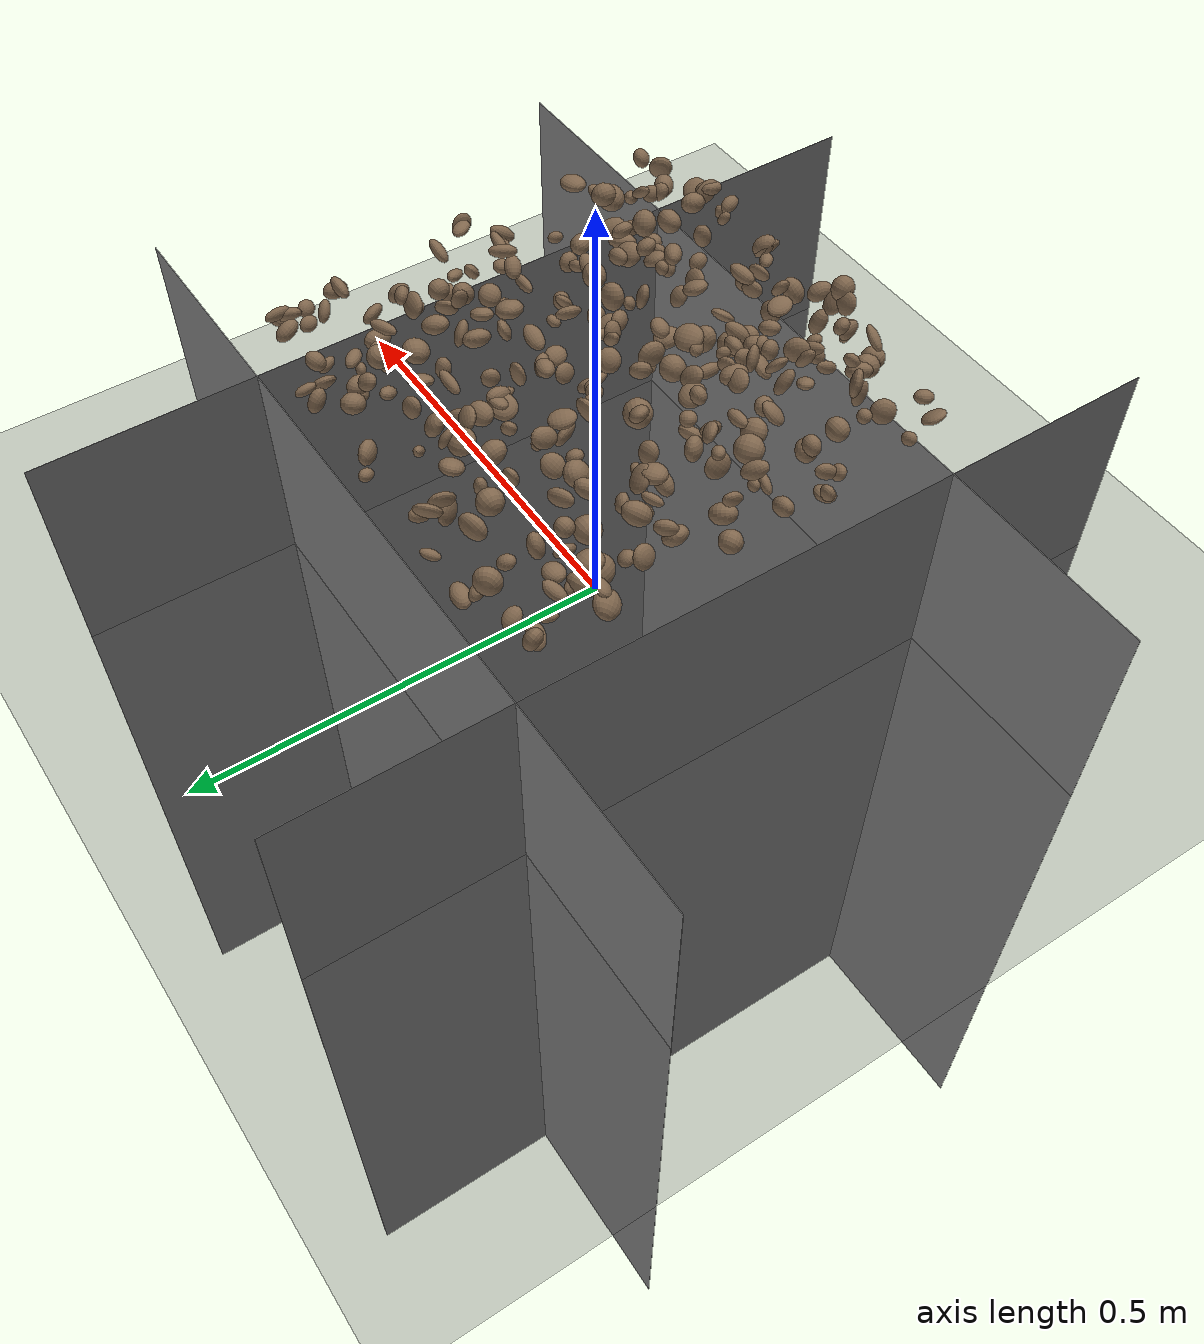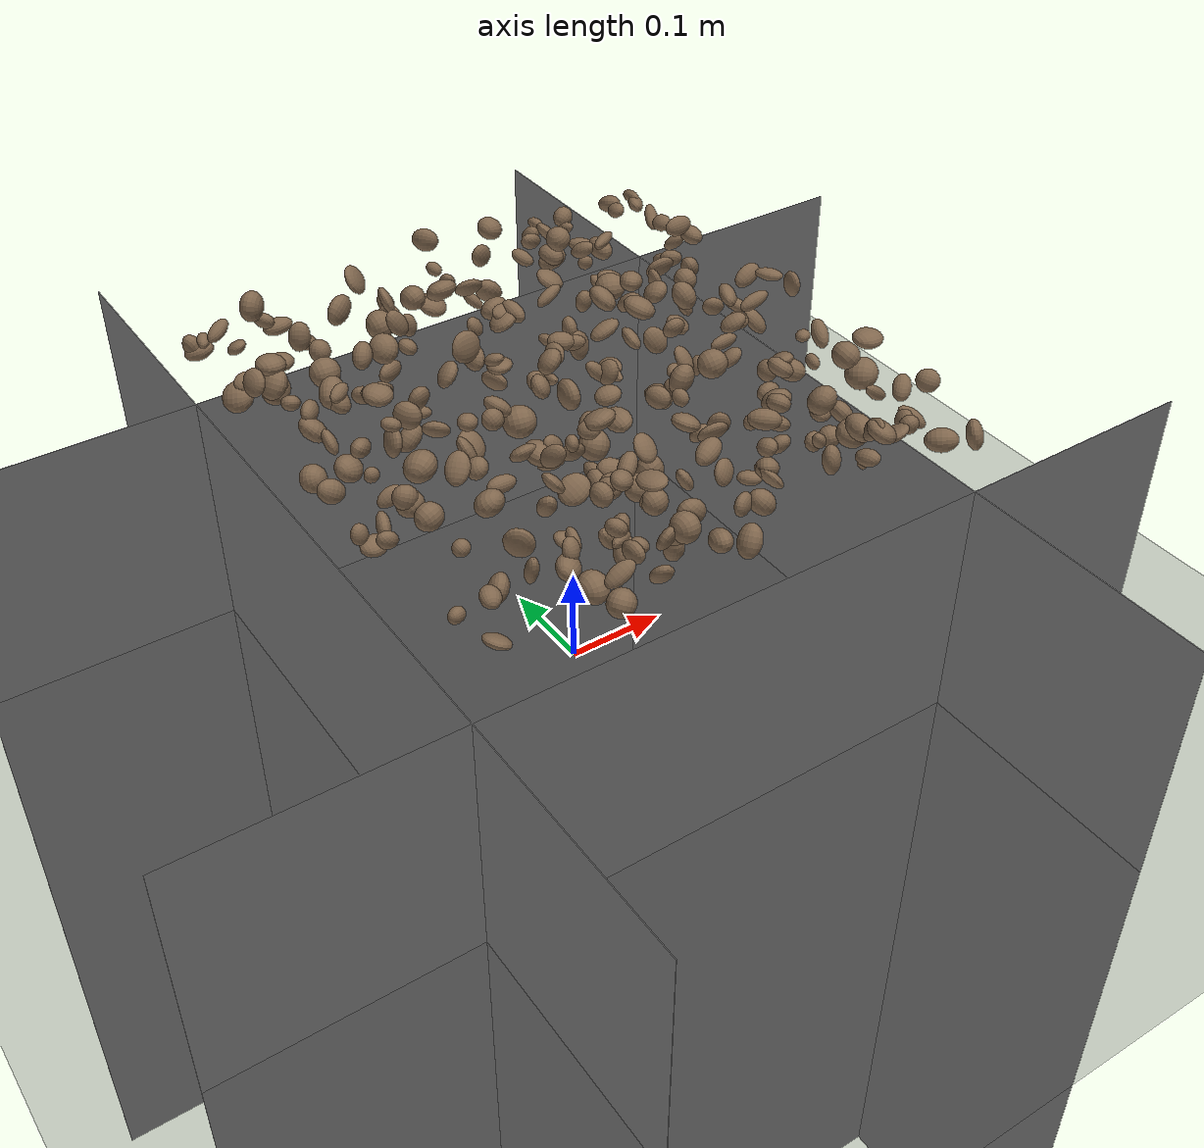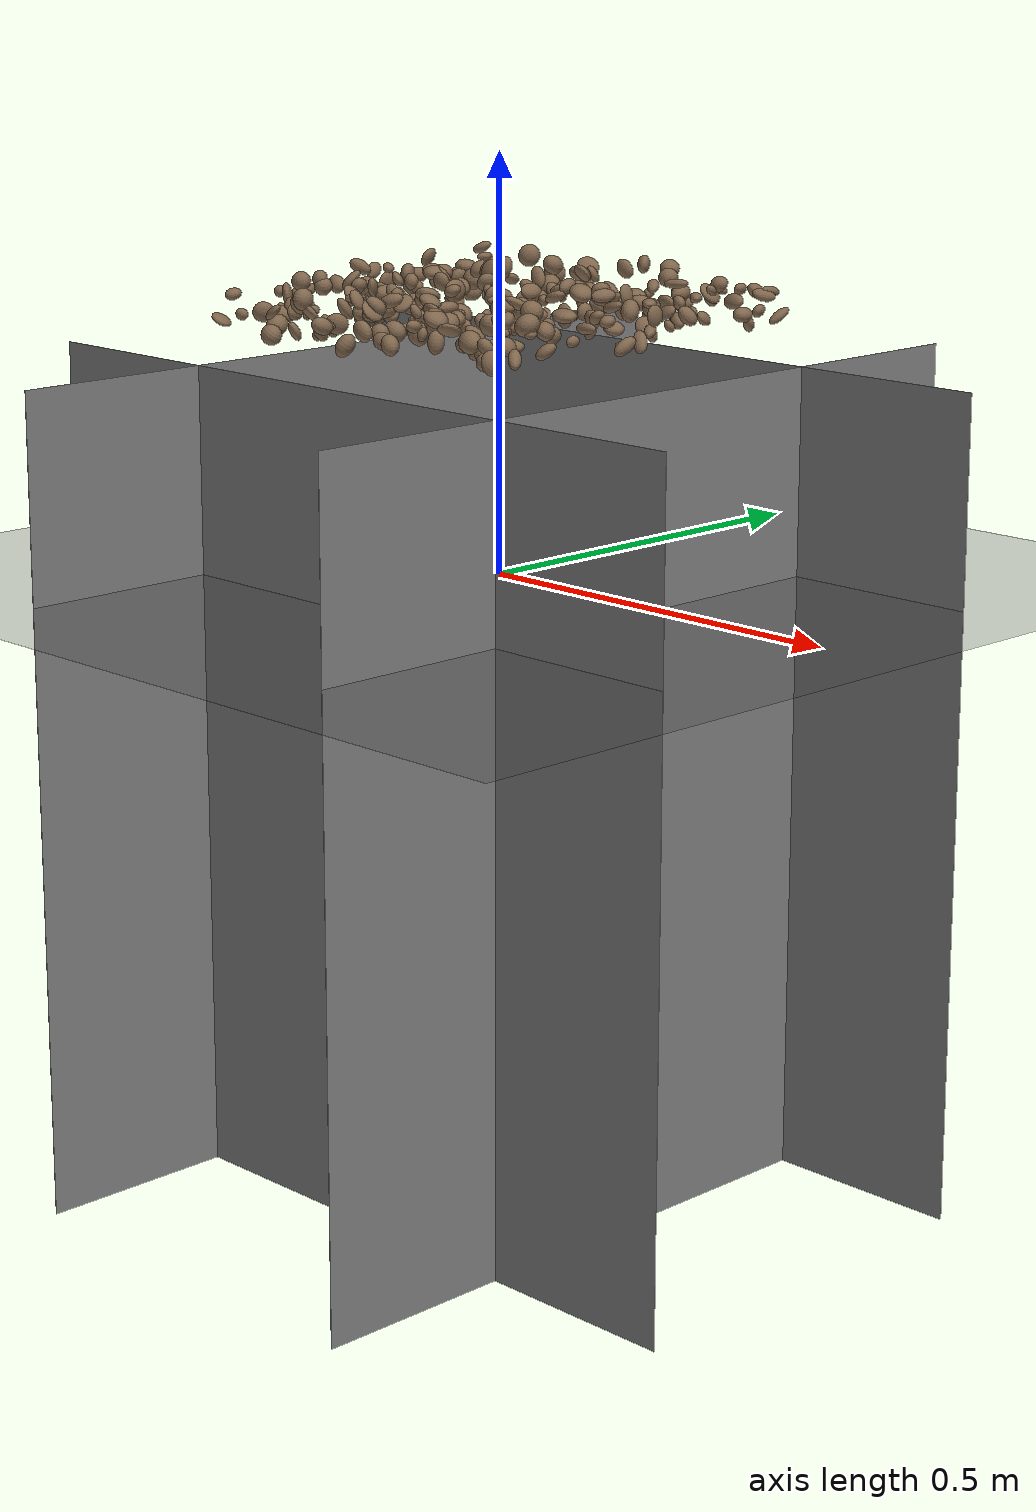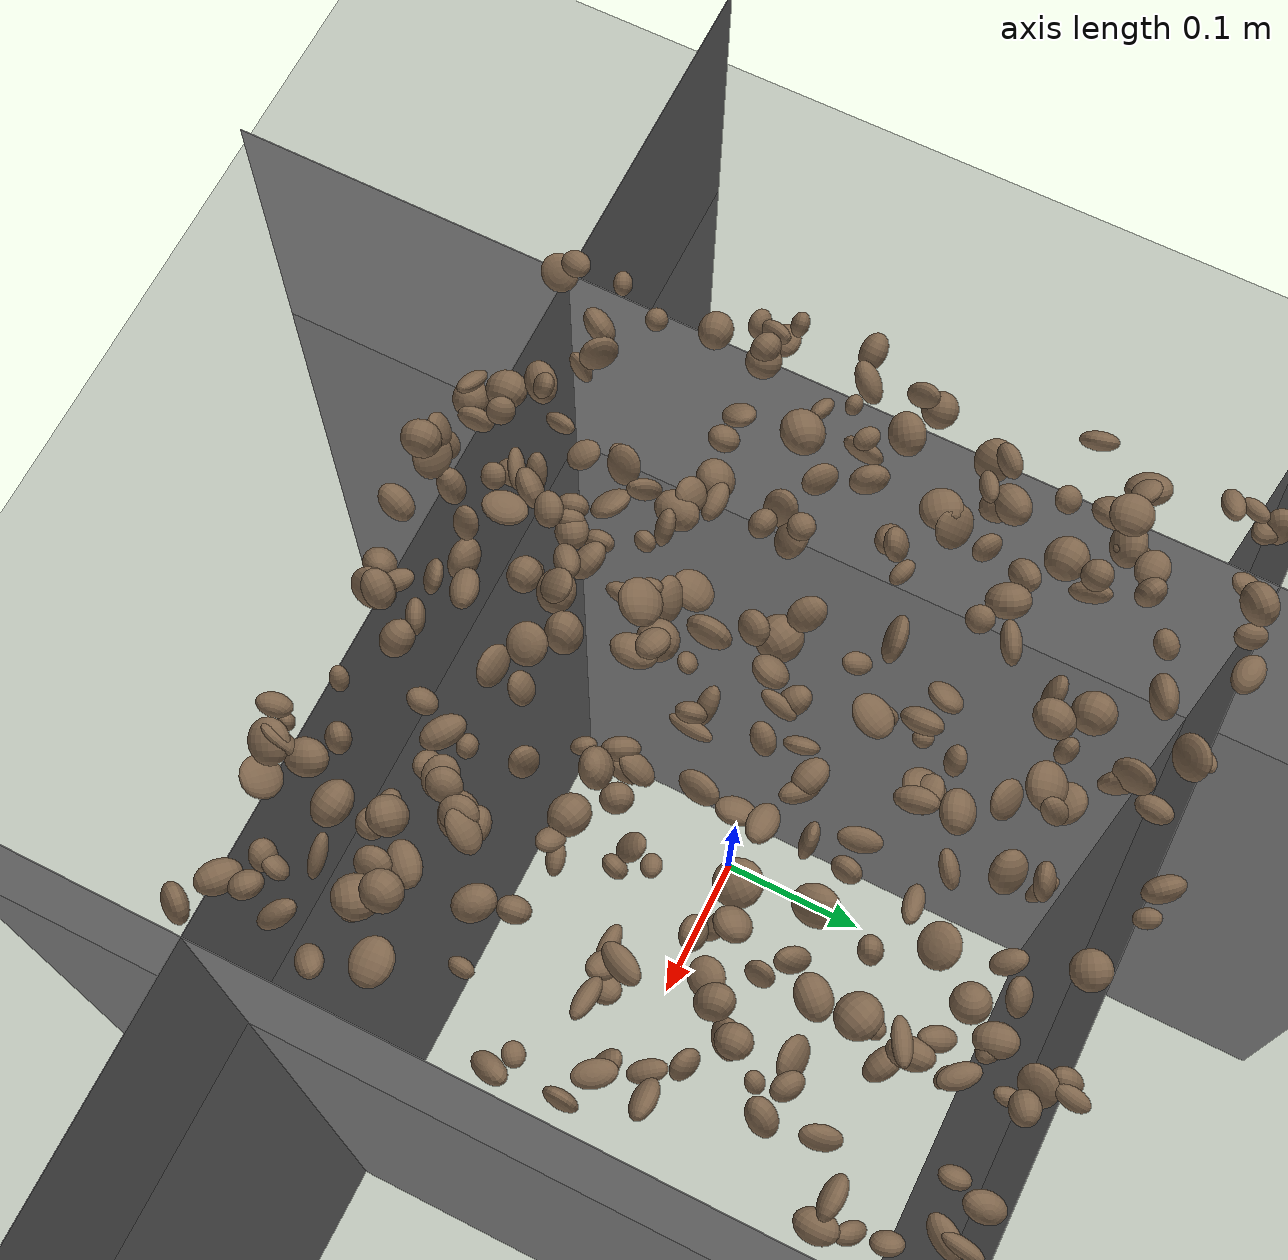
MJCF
<mujoco model="rocky_terrain_scene">

  <default>
    <default class="wall">
      <geom type="plane" size=".5 .5 .05" />
    </default>
  </default>

    <compiler angle="radian" inertiafromgeom="true" />
    <option timestep="0.002" gravity="0 0 -9.81" />

    <worldbody>

        <geom name="+x" class="wall" zaxis="1 0 0" pos="-.25 0 -.25" />
        <geom name="-x" class="wall" zaxis="-1 0 0" pos=".25 0 -.25" />
        <geom name="+y" class="wall" zaxis="0 1 0" pos="0 -.25 -.25" />
        <geom name="-y" class="wall" zaxis="0 -1 0" pos="0 .25 -.25" />

        <light name="sunlight" pos="5 5 5" dir="-1 -1 -1" diffuse="1 1 1" specular="0.5 0.5 0.5" ambient="0.5 0.5 0.5" />

        <geom name="ground_plane" type="plane" size="50 50 0.1" rgba="0.3 0.3 0.3 1" />

        <body name="rocky_terrain_body">

        </body>
    <body name="rock1" pos="0.1274987104949465 -0.061954537437645396 0.3316263140595676"><joint type="free" /><geom type="ellipsoid" size="0.005652509432562073 0.006623343959060759 0.010471830601010167" quat="0.2095541861625089 0.2041186089832849 0.35427722866659594 0.2320499761876104" rgba="0.5 0.4 0.3 1" /><inertial pos="0.1274987104949465 -0.061954537437645396 0.3316263140595676" quat="0.2095541861625089 0.2041186089832849 0.35427722866659594 0.2320499761876104" mass="6.0188091419262975e-05" /></body><body name="rock2" pos="-0.03983620059138354 -0.08839450924959008 0.3338984851162777"><joint type="free" /><geom type="ellipsoid" size="0.00989495116042954 0.00819355563519377 0.006469544133514492" quat="0.1318467359390663 0.17155004437554697 0.4911610088083072 0.20544221087707942" rgba="0.5 0.4 0.3 1" /><inertial pos="-0.03983620059138354 -0.08839450924959008 0.3338984851162777" quat="0.1318467359390663 0.17155004437554697 0.4911610088083072 0.20544221087707942" mass="7.20234146084338e-05" /></body><body name="rock3" pos="-0.11342026364636831 -0.16778317759114325 0.30396059614052023"><joint type="free" /><geom type="ellipsoid" size="0.011249839983319129 0.0056614173756784885 0.009013661380929301" quat="0.06129119248195876 0.2143972424669908 0.34218017202897916 0.3821313930220712" rgba="0.5 0.4 0.3 1" /><inertial pos="-0.11342026364636831 -0.16778317759114325 0.30396059614052023" quat="0.06129119248195876 0.2143972424669908 0.34218017202897916 0.3821313930220712" mass="4.353183407230963e-05" /></body><body name="rock4" pos="0.19089352762272394 -0.13603561135190156 0.34859531352896816"><joint type="free" /><geom type="ellipsoid" size="0.012985379766185228 0.012635600801865035 0.011598881665550516" quat="0.3717328862237738 0.1569922799206901 0.15415542161912033 0.3171194122364159" rgba="0.5 0.4 0.3 1" /><inertial pos="0.19089352762272394 -0.13603561135190156 0.34859531352896816" quat="0.3717328862237738 0.1569922799206901 0.15415542161912033 0.3171194122364159" mass="1.155152340263901e-05" /></body><body name="rock5" pos="-0.021203475598340737 -0.0004612905305045878 0.3465160974144231"><joint type="free" /><geom type="ellipsoid" size="0.011766963087907527 0.01239456522847418 0.008016117528287755" quat="0.18998951403870798 0.41610128504619076 0.2611863895676018 0.1327228113474995" rgba="0.5 0.4 0.3 1" /><inertial pos="-0.021203475598340737 -0.0004612905305045878 0.3465160974144231" quat="0.18998951403870798 0.41610128504619076 0.2611863895676018 0.1327228113474995" mass="1.55690772205833e-05" /></body><body name="rock6" pos="0.07009297269767223 -0.06576452938713495 0.33063780116828273"><joint type="free" /><geom type="ellipsoid" size="0.01271823761530313 0.009865018179063812 0.01437276525082105" quat="0.6942758674572022 0.07567382158601368 0.07304509837304868 0.15700521258373543" rgba="0.5 0.4 0.3 1" /><inertial pos="0.07009297269767223 -0.06576452938713495 0.33063780116828273" quat="0.6942758674572022 0.07567382158601368 0.07304509837304868 0.15700521258373543" mass="3.7046149446070466e-05" /></body><body name="rock7" pos="-0.05588080402851203 -0.22819354447700568 0.31138409646385784"><joint type="free" /><geom type="ellipsoid" size="0.008604521195874876 0.008676178441250614 0.014388138486042049" quat="0.013675634367430658 0.2254435181216828 0.6490162102671753 0.1118646372437112" rgba="0.5 0.4 0.3 1" /><inertial pos="-0.05588080402851203 -0.22819354447700568 0.31138409646385784" quat="0.013675634367430658 0.2254435181216828 0.6490162102671753 0.1118646372437112" mass="9.755848167607246e-05" /></body><body name="rock8" pos="-0.07883075913880128 -0.09561530646385474 0.3370077051664353"><joint type="free" /><geom type="ellipsoid" size="0.008725969667597287 0.0056463311005798865 0.012061303376596843" quat="0.03973101317440436 0.6048697545530474 0.13817873854662652 0.2172204937259218" rgba="0.5 0.4 0.3 1" /><inertial pos="-0.07883075913880128 -0.09561530646385474 0.3370077051664353" quat="0.03973101317440436 0.6048697545530474 0.13817873854662652 0.2172204937259218" mass="1.6038235655871886e-05" /></body><body name="rock9" pos="-0.1579656774725619 -0.00029075409142437225 0.343289930092876"><joint type="free" /><geom type="ellipsoid" size="0.008304112606182572 0.012427693809525783 0.012090326204836402" quat="0.6691942961276578 0.04447385283178099 0.05748377310485318 0.22884807793570816" rgba="0.5 0.4 0.3 1" /><inertial pos="-0.1579656774725619 -0.00029075409142437225 0.343289930092876" quat="0.6691942961276578 0.04447385283178099 0.05748377310485318 0.22884807793570816" mass="9.061456355795799e-05" /></body><body name="rock10" pos="-0.09195054891639104 0.17515122539643935 0.31867883275445563"><joint type="free" /><geom type="ellipsoid" size="0.013632488362925566 0.013861927779150872 0.012766358328701238" quat="0.32636997973211307 0.189871177248266 0.27138525293913696 0.21237359008048395" rgba="0.5 0.4 0.3 1" /><inertial pos="-0.09195054891639104 0.17515122539643935 0.31867883275445563" quat="0.32636997973211307 0.189871177248266 0.27138525293913696 0.21237359008048395" mass="6.523008823488943e-05" /></body><body name="rock11" pos="0.20303078680281822 -0.15077714585649704 0.32663264224969596"><joint type="free" /><geom type="ellipsoid" size="0.007794114429963988 0.00571859025178397 0.007659558177498612" quat="0.12440305979909907 0.21355241223566857 0.3387788534996268 0.32326567446560556" rgba="0.5 0.4 0.3 1" /><inertial pos="0.20303078680281822 -0.15077714585649704 0.32663264224969596" quat="0.12440305979909907 0.21355241223566857 0.3387788534996268 0.32326567446560556" mass="6.98202538239627e-05" /></body><body name="rock12" pos="0.1478765366710415 -0.15803237084526167 0.33115841651682715"><joint type="free" /><geom type="ellipsoid" size="0.011224678149618396 0.0137714070119236 0.012264876235135778" quat="0.033273062476307666 0.3103483620984238 0.3118634090839064 0.3445151663413621" rgba="0.5 0.4 0.3 1" /><inertial pos="0.1478765366710415 -0.15803237084526167 0.33115841651682715" quat="0.033273062476307666 0.3103483620984238 0.3118634090839064 0.3445151663413621" mass="5.166807336743858e-05" /></body><body name="rock13" pos="-0.02823338266023323 -0.24998661849443177 0.32041710103133386"><joint type="free" /><geom type="ellipsoid" size="0.009743440744283374 0.013143243268797993 0.00930159893033532" quat="0.14687375684461929 0.4114337542743608 0.026774687641544666 0.41491780123947525" rgba="0.5 0.4 0.3 1" /><inertial pos="-0.02823338266023323 -0.24998661849443177 0.32041710103133386" quat="0.14687375684461929 0.4114337542743608 0.026774687641544666 0.41491780123947525" mass="9.715830167551516e-05" /></body><body name="rock14" pos="0.1252039086840281 0.1696485946404585 0.3318124277275541"><joint type="free" /><geom type="ellipsoid" size="0.007760076759084068 0.00726684013927255 0.012769532413058683" quat="0.475284003690444 0.2853191638839566 0.06068239739886159 0.1787144350267378" rgba="0.5 0.4 0.3 1" /><inertial pos="0.1252039086840281 0.1696485946404585 0.3318124277275541" quat="0.475284003690444 0.2853191638839566 0.06068239739886159 0.1787144350267378" mass="4.944486954133732e-05" /></body><body name="rock15" pos="-0.19280024643427152 -0.1970567057674495 0.31357965461655657"><joint type="free" /><geom type="ellipsoid" size="0.01290759489063063 0.012736477978692737 0.008075394101614442" quat="0.31830068122926114 0.296990068085463 0.34009231427545905 0.04461693640981682" rgba="0.5 0.4 0.3 1" /><inertial pos="-0.19280024643427152 -0.1970567057674495 0.31357965461655657" quat="0.31830068122926114 0.296990068085463 0.34009231427545905 0.04461693640981682" mass="7.033175877307668e-05" /></body><body name="rock16" pos="0.2375636681025995 -0.16074711996595087 0.31230395337349653"><joint type="free" /><geom type="ellipsoid" size="0.013005063941811525 0.007061696752361837 0.00837086819407972" quat="0.2789396011879668 0.42400931591773533 0.04655382807002676 0.2504972548242711" rgba="0.5 0.4 0.3 1" /><inertial pos="0.2375636681025995 -0.16074711996595087 0.31230395337349653" quat="0.2789396011879668 0.42400931591773533 0.04655382807002676 0.2504972548242711" mass="1.8163873055438744e-05" /></body><body name="rock17" pos="-0.17035706807459966 0.17563716763390164 0.33271975047091784"><joint type="free" /><geom type="ellipsoid" size="0.00811534101206665 0.013905114597961704 0.0098725538986559" quat="0.31241362669137396 0.3151195252926369 0.2253582830540044 0.14710856496198457" rgba="0.5 0.4 0.3 1" /><inertial pos="-0.17035706807459966 0.17563716763390164 0.33271975047091784" quat="0.31241362669137396 0.3151195252926369 0.2253582830540044 0.14710856496198457" mass="8.316304603082001e-05" /></body><body name="rock18" pos="0.004837179280988202 0.032603566210053225 0.32778449433974277"><joint type="free" /><geom type="ellipsoid" size="0.01096257777146973 0.01014817895083757 0.005214632055248747" quat="0.15389049650901918 0.3042683230988113 0.3030659767054416 0.23877520368672794" rgba="0.5 0.4 0.3 1" /><inertial pos="0.004837179280988202 0.032603566210053225 0.32778449433974277" quat="0.15389049650901918 0.3042683230988113 0.3030659767054416 0.23877520368672794" mass="6.864393070898612e-05" /></body><body name="rock19" pos="0.08887098459497556 -0.1392866023637948 0.3212921890798399"><joint type="free" /><geom type="ellipsoid" size="0.006427088164779032 0.007575196785462403 0.007398676983080388" quat="0.25353240918970193 0.23816043638005888 0.20633569406338648 0.3019714603668528" rgba="0.5 0.4 0.3 1" /><inertial pos="0.08887098459497556 -0.1392866023637948 0.3212921890798399" quat="0.25353240918970193 0.23816043638005888 0.20633569406338648 0.3019714603668528" mass="5.247116449203029e-05" /></body><body name="rock20" pos="-0.20764120682876186 0.15335469177531708 0.3033150124587806"><joint type="free" /><geom type="ellipsoid" size="0.010271758223005377 0.013859883809212024 0.014752928234347241" quat="0.2720829034764698 0.133548850849079 0.3415361373374389 0.25283210833701236" rgba="0.5 0.4 0.3 1" /><inertial pos="-0.20764120682876186 0.15335469177531708 0.3033150124587806" quat="0.2720829034764698 0.133548850849079 0.3415361373374389 0.25283210833701236" mass="8.156357444921028e-05" /></body><body name="rock21" pos="0.04346197693114112 -0.12797822761720073 0.32075496163013306"><joint type="free" /><geom type="ellipsoid" size="0.00588009942602684 0.01161405907696763 0.009510372732211773" quat="0.20142451222817695 0.299185735895137 0.15382537322798023 0.3455643786487058" rgba="0.5 0.4 0.3 1" /><inertial pos="0.04346197693114112 -0.12797822761720073 0.32075496163013306" quat="0.20142451222817695 0.299185735895137 0.15382537322798023 0.3455643786487058" mass="7.214309461416281e-05" /></body><body name="rock22" pos="-0.24634792101693853 0.22405170354734966 0.31937709926388813"><joint type="free" /><geom type="ellipsoid" size="0.00873773307304062 0.013554625397388664 0.007669139724899276" quat="0.05199935926831435 0.5084425214675764 0.3570314161902719 0.08252670307383728" rgba="0.5 0.4 0.3 1" /><inertial pos="-0.24634792101693853 0.22405170354734966 0.31937709926388813" quat="0.05199935926831435 0.5084425214675764 0.3570314161902719 0.08252670307383728" mass="7.72225090080604e-05" /></body><body name="rock23" pos="0.11785064132985085 0.08051435279953406 0.3193383720398605"><joint type="free" /><geom type="ellipsoid" size="0.013753786245030195 0.006393453362059889 0.009048473073307545" quat="0.28173873311170583 0.2040023725773258 0.5020518659631725 0.01220702834779584" rgba="0.5 0.4 0.3 1" /><inertial pos="0.11785064132985085 0.08051435279953406 0.3193383720398605" quat="0.28173873311170583 0.2040023725773258 0.5020518659631725 0.01220702834779584" mass="8.919223271394982e-05" /></body><body name="rock24" pos="-0.11956674029791048 -0.08135080070890593 0.30777347350245327"><joint type="free" /><geom type="ellipsoid" size="0.006992746636881528 0.007415201759023523 0.013360550109169242" quat="0.3373567336181223 0.15708540489155193 0.35314997035953627 0.15240789113078954" rgba="0.5 0.4 0.3 1" /><inertial pos="-0.11956674029791048 -0.08135080070890593 0.30777347350245327" quat="0.3373567336181223 0.15708540489155193 0.35314997035953627 0.15240789113078954" mass="8.325866785998497e-05" /></body><body name="rock25" pos="-0.16525676479192591 -0.18318623853385485 0.33512009635469553"><joint type="free" /><geom type="ellipsoid" size="0.012583501398740024 0.014569101931463702 0.005873102616546704" quat="0.12584134035169287 0.15459865415749754 0.32772409160973404 0.3918359138810755" rgba="0.5 0.4 0.3 1" /><inertial pos="-0.16525676479192591 -0.18318623853385485 0.33512009635469553" quat="0.12584134035169287 0.15459865415749754 0.32772409160973404 0.3918359138810755" mass="1.2160238917152794e-05" /></body><body name="rock26" pos="0.1396580671081326 0.22615276049810262 0.3382197672726842"><joint type="free" /><geom type="ellipsoid" size="0.008921345065967961 0.009394604389690309 0.010580489645459542" quat="0.31065896628117234 0.0856156228560105 0.27860554411610894 0.3251198667467082" rgba="0.5 0.4 0.3 1" /><inertial pos="0.1396580671081326 0.22615276049810262 0.3382197672726842" quat="0.31065896628117234 0.0856156228560105 0.27860554411610894 0.3251198667467082" mass="1.1524856490611297e-05" /></body><body name="rock27" pos="0.1116109068447192 0.24270272080056293 0.31813004675693307"><joint type="free" /><geom type="ellipsoid" size="0.0083274370563002 0.013248530723002798 0.007685100276219428" quat="0.1270700767965224 0.2806780138826482 0.21524173036157382 0.37701017895925554" rgba="0.5 0.4 0.3 1" /><inertial pos="0.1116109068447192 0.24270272080056293 0.31813004675693307" quat="0.1270700767965224 0.2806780138826482 0.21524173036157382 0.37701017895925554" mass="6.769823281954438e-05" /></body><body name="rock28" pos="-0.2492468665250166 0.22893384931317906 0.32196926339691573"><joint type="free" /><geom type="ellipsoid" size="0.009976270710392844 0.013414185693060084 0.008116452948194592" quat="0.23918470920723905 0.1708516271882019 0.24569438311284242 0.3442692804917165" rgba="0.5 0.4 0.3 1" /><inertial pos="-0.2492468665250166 0.22893384931317906 0.32196926339691573" quat="0.23918470920723905 0.1708516271882019 0.24569438311284242 0.3442692804917165" mass="5.845496572903532e-05" /></body><body name="rock29" pos="-0.04370625086329566 -0.10279680342046815 0.3004535911370527"><joint type="free" /><geom type="ellipsoid" size="0.014369510404811717 0.006365109164429519 0.007496601515290124" quat="0.46067812760880184 0.04419564812324348 0.0272961623121798 0.46783006195577487" rgba="0.5 0.4 0.3 1" /><inertial pos="-0.04370625086329566 -0.10279680342046815 0.3004535911370527" quat="0.46067812760880184 0.04419564812324348 0.0272961623121798 0.46783006195577487" mass="9.440757994477302e-05" /></body><body name="rock30" pos="0.12721094517370235 -0.1244762962098866 0.3200447405026198"><joint type="free" /><geom type="ellipsoid" size="0.009849694118903525 0.01343833741042836 0.01443454703460791" quat="0.03851390858866085 0.38806198209392906 0.24098526563044506 0.3324388436869651" rgba="0.5 0.4 0.3 1" /><inertial pos="0.12721094517370235 -0.1244762962098866 0.3200447405026198" quat="0.03851390858866085 0.38806198209392906 0.24098526563044506 0.3324388436869651" mass="7.65932945690144e-05" /></body><body name="rock31" pos="0.09782955636641388 0.036216381890007865 0.3421419383564711"><joint type="free" /><geom type="ellipsoid" size="0.014226370818008763 0.009310343504086542 0.014761562078985858" quat="0.30267389718501925 0.4009767539772708 0.21327809654957436 0.08307125228813554" rgba="0.5 0.4 0.3 1" /><inertial pos="0.09782955636641388 0.036216381890007865 0.3421419383564711" quat="0.30267389718501925 0.4009767539772708 0.21327809654957436 0.08307125228813554" mass="7.837109528763554e-05" /></body><body name="rock32" pos="-0.2353309862937602 0.1976964780515636 0.34974729459742915"><joint type="free" /><geom type="ellipsoid" size="0.00720198795552013 0.012801306664531473 0.006109920152639242" quat="0.10023739068315492 0.3229168717708139 0.4885648049558993 0.08828093259013194" rgba="0.5 0.4 0.3 1" /><inertial pos="-0.2353309862937602 0.1976964780515636 0.34974729459742915" quat="0.10023739068315492 0.3229168717708139 0.4885648049558993 0.08828093259013194" mass="1.116550387465469e-05" /></body><body name="rock33" pos="-0.06656211350181584 0.21016902774769475 0.31899858889097954"><joint type="free" /><geom type="ellipsoid" size="0.013730366654596867 0.012814357492939892 0.00539787268964945" quat="0.245231607579162 0.28878522812041807 0.10816151564625442 0.35782164865416544" rgba="0.5 0.4 0.3 1" /><inertial pos="-0.06656211350181584 0.21016902774769475 0.31899858889097954" quat="0.245231607579162 0.28878522812041807 0.10816151564625442 0.35782164865416544" mass="2.497128107810683e-05" /></body><body name="rock34" pos="0.17208417589338837 -0.15660638074312122 0.30991409374030693"><joint type="free" /><geom type="ellipsoid" size="0.011841702449266762 0.011481206168912666 0.008003557941060054" quat="0.26540711499917913 0.20273058889319698 0.12580856132882978 0.4060537347787942" rgba="0.5 0.4 0.3 1" /><inertial pos="0.17208417589338837 -0.15660638074312122 0.30991409374030693" quat="0.26540711499917913 0.20273058889319698 0.12580856132882978 0.4060537347787942" mass="7.722632841603767e-05" /></body><body name="rock35" pos="-0.0025119137936520652 0.10594667171960015 0.32863339785399287"><joint type="free" /><geom type="ellipsoid" size="0.01384190157254686 0.014810037006373154 0.006639241442813779" quat="0.1501736296043443 0.30959593254964224 0.5089565156527346 0.03127392219327883" rgba="0.5 0.4 0.3 1" /><inertial pos="-0.0025119137936520652 0.10594667171960015 0.32863339785399287" quat="0.1501736296043443 0.30959593254964224 0.5089565156527346 0.03127392219327883" mass="5.763823502075141e-05" /></body><body name="rock36" pos="0.10270639921365138 0.17750758921853416 0.3468381375391403"><joint type="free" /><geom type="ellipsoid" size="0.011692148895928647 0.011749729186485881 0.011381161910875015" quat="0.028675353083920423 0.45766068843856306 0.3783525660293257 0.13531139244819085" rgba="0.5 0.4 0.3 1" /><inertial pos="0.10270639921365138 0.17750758921853416 0.3468381375391403" quat="0.028675353083920423 0.45766068843856306 0.3783525660293257 0.13531139244819085" mass="8.26725235068759e-05" /></body><body name="rock37" pos="0.22109579321992984 -0.2043105523692938 0.34874414247823593"><joint type="free" /><geom type="ellipsoid" size="0.008004217237991742 0.010119162246787244 0.010339926318743801" quat="0.34397418117762896 0.3569377547951812 0.2719212413129379 0.027166822714251974" rgba="0.5 0.4 0.3 1" /><inertial pos="0.22109579321992984 -0.2043105523692938 0.34874414247823593" quat="0.34397418117762896 0.3569377547951812 0.2719212413129379 0.027166822714251974" mass="1.8399654716498286e-05" /></body><body name="rock38" pos="0.1997973320609861 -0.2031442061317847 0.3179425975844942"><joint type="free" /><geom type="ellipsoid" size="0.00890706609439756 0.00935942663999471 0.005887931867033215" quat="0.14380649906914478 0.540019308598705 0.023881537869167562 0.2922926544629828" rgba="0.5 0.4 0.3 1" /><inertial pos="0.1997973320609861 -0.2031442061317847 0.3179425975844942" quat="0.14380649906914478 0.540019308598705 0.023881537869167562 0.2922926544629828" mass="3.585733219031789e-05" /></body><body name="rock39" pos="-0.13360945679065372 -0.20479764487429802 0.3290193551381372"><joint type="free" /><geom type="ellipsoid" size="0.005874583749667962 0.010080879781586116 0.008088401525577512" quat="0.2394505311760642 0.17536100034078012 0.3826906630414296 0.2024978054417261" rgba="0.5 0.4 0.3 1" /><inertial pos="-0.13360945679065372 -0.20479764487429802 0.3290193551381372" quat="0.2394505311760642 0.17536100034078012 0.3826906630414296 0.2024978054417261" mass="8.847208098249689e-05" /></body><body name="rock40" pos="-0.1675761055408636 0.1447960834133194 0.3048395634696007"><joint type="free" /><geom type="ellipsoid" size="0.007485698243978965 0.013795172119176389 0.005756548927427553" quat="0.4733430541633134 0.06474777151193342 0.3518979888609346 0.1100111854638185" rgba="0.5 0.4 0.3 1" /><inertial pos="-0.1675761055408636 0.1447960834133194 0.3048395634696007" quat="0.4733430541633134 0.06474777151193342 0.3518979888609346 0.1100111854638185" mass="6.785700399466226e-05" /></body><body name="rock41" pos="0.19770235255170682 -0.15006617457027238 0.3354430328005261"><joint type="free" /><geom type="ellipsoid" size="0.014699560153917032 0.012417286346951686 0.014278184364605442" quat="0.36699170395592046 0.3759800294166501 0.011347254136008953 0.24568101249142044" rgba="0.5 0.4 0.3 1" /><inertial pos="0.19770235255170682 -0.15006617457027238 0.3354430328005261" quat="0.36699170395592046 0.3759800294166501 0.011347254136008953 0.24568101249142044" mass="6.844068316308637e-05" /></body><body name="rock42" pos="0.010537355217386468 -0.20200815977140163 0.3393962944900166"><joint type="free" /><geom type="ellipsoid" size="0.011433926307940444 0.005180407910532624 0.01047460640422853" quat="0.068217153065315 0.5674273686573388 0.1450256648276591 0.219329813449687" rgba="0.5 0.4 0.3 1" /><inertial pos="0.010537355217386468 -0.20200815977140163 0.3393962944900166" quat="0.068217153065315 0.5674273686573388 0.1450256648276591 0.219329813449687" mass="3.494793894275495e-05" /></body><body name="rock43" pos="-0.20694587614899562 -0.09175556336335355 0.33174185132867196"><joint type="free" /><geom type="ellipsoid" size="0.01099017198207823 0.010932095606556204 0.011709738612147975" quat="0.336558452028868 0.2622801626135693 0.037075069289391756 0.3640863160681709" rgba="0.5 0.4 0.3 1" /><inertial pos="-0.20694587614899562 -0.09175556336335355 0.33174185132867196" quat="0.336558452028868 0.2622801626135693 0.037075069289391756 0.3640863160681709" mass="4.401619492628372e-05" /></body><body name="rock44" pos="0.20236751354983346 -0.08330155605300493 0.3106505277936201"><joint type="free" /><geom type="ellipsoid" size="0.008548377301030889 0.006535403597560916 0.005400584078476821" quat="0.24523377307153899 0.28603610890299475 0.20514392470090745 0.2635861933245588" rgba="0.5 0.4 0.3 1" /><inertial pos="0.20236751354983346 -0.08330155605300493 0.3106505277936201" quat="0.24523377307153899 0.28603610890299475 0.20514392470090745 0.2635861933245588" mass="4.973764925782267e-05" /></body><body name="rock45" pos="0.08778976644336456 0.07986933526638335 0.3337055390750331"><joint type="free" /><geom type="ellipsoid" size="0.008912717208488349 0.014714144757811461 0.013058990213608252" quat="0.26716066529489785 0.02437732654170386 0.6287036289248776 0.0797583792385207" rgba="0.5 0.4 0.3 1" /><inertial pos="0.08778976644336456 0.07986933526638335 0.3337055390750331" quat="0.26716066529489785 0.02437732654170386 0.6287036289248776 0.0797583792385207" mass="4.797834446710022e-05" /></body><body name="rock46" pos="-0.245162916236218 0.21161242777843603 0.336392823425391"><joint type="free" /><geom type="ellipsoid" size="0.0057428927627279965 0.009993218708373372 0.005247710886649373" quat="0.05378293086900296 0.1469657489046707 0.7817507868598873 0.01750053336643905" rgba="0.5 0.4 0.3 1" /><inertial pos="-0.245162916236218 0.21161242777843603 0.336392823425391" quat="0.05378293086900296 0.1469657489046707 0.7817507868598873 0.01750053336643905" mass="9.789159839624521e-05" /></body><body name="rock47" pos="-0.0923862035819703 -0.09441621414578988 0.3352807159741751"><joint type="free" /><geom type="ellipsoid" size="0.014566159158734594 0.011520559814521526 0.00966621695286229" quat="0.45763496017503186 0.07224546963615022 0.0850330876287763 0.38508648256004163" rgba="0.5 0.4 0.3 1" /><inertial pos="-0.0923862035819703 -0.09441621414578988 0.3352807159741751" quat="0.45763496017503186 0.07224546963615022 0.0850330876287763 0.38508648256004163" mass="6.89837989822698e-05" /></body><body name="rock48" pos="-0.10390559683158335 -0.04444123117947485 0.3436514798324278"><joint type="free" /><geom type="ellipsoid" size="0.007887883935325992 0.009648389078415557 0.009263812125404568" quat="0.357597787863001 0.16948631193191163 0.21659236389906442 0.2563235363060229" rgba="0.5 0.4 0.3 1" /><inertial pos="-0.10390559683158335 -0.04444123117947485 0.3436514798324278" quat="0.357597787863001 0.16948631193191163 0.21659236389906442 0.2563235363060229" mass="6.017195267825186e-05" /></body><body name="rock49" pos="-0.029859445947899466 -0.04313270990050988 0.3396812110331381"><joint type="free" /><geom type="ellipsoid" size="0.013656447790293617 0.014418322945322425 0.0078706505419175" quat="0.05120961858424521 0.4706646075787187 0.030694101322065674 0.4474316725149704" rgba="0.5 0.4 0.3 1" /><inertial pos="-0.029859445947899466 -0.04313270990050988 0.3396812110331381" quat="0.05120961858424521 0.4706646075787187 0.030694101322065674 0.4474316725149704" mass="1.888185473953301e-05" /></body><body name="rock50" pos="-0.229580824736127 -0.1990657644507967 0.30713409382570284"><joint type="free" /><geom type="ellipsoid" size="0.006038549988985561 0.007157205174248354 0.00788079693776737" quat="0.14094123243345497 0.2633991252188915 0.3182733390909165 0.277386303256737" rgba="0.5 0.4 0.3 1" /><inertial pos="-0.229580824736127 -0.1990657644507967 0.30713409382570284" quat="0.14094123243345497 0.2633991252188915 0.3182733390909165 0.277386303256737" mass="1.0736384453282117e-05" /></body><body name="rock51" pos="-0.20359957368888676 -0.049364982549270575 0.3106606927871734"><joint type="free" /><geom type="ellipsoid" size="0.005312187765419048 0.011983406839554355 0.007314166707050793" quat="0.21248659828823466 0.44262854624598086 0.34075695369292064 0.004127901772863832" rgba="0.5 0.4 0.3 1" /><inertial pos="-0.20359957368888676 -0.049364982549270575 0.3106606927871734" quat="0.21248659828823466 0.44262854624598086 0.34075695369292064 0.004127901772863832" mass="6.700024988263775e-05" /></body><body name="rock52" pos="0.20774229645704134 0.035224965645229644 0.31018140412671935"><joint type="free" /><geom type="ellipsoid" size="0.012433757127639004 0.005905637718478134 0.00686970189938918" quat="0.10498947799668512 0.23792129386933875 0.3163310277036159 0.34075820043036026" rgba="0.5 0.4 0.3 1" /><inertial pos="0.20774229645704134 0.035224965645229644 0.31018140412671935" quat="0.10498947799668512 0.23792129386933875 0.3163310277036159 0.34075820043036026" mass="9.260966904184151e-05" /></body><body name="rock53" pos="0.24441410110328093 -0.04384425167266476 0.30558707230292703"><joint type="free" /><geom type="ellipsoid" size="0.007706106438435159 0.014790885989705398 0.007976581101402888" quat="0.02342930327370932 0.10634585907431171 0.6645136687925387 0.20571116885944019" rgba="0.5 0.4 0.3 1" /><inertial pos="0.24441410110328093 -0.04384425167266476 0.30558707230292703" quat="0.02342930327370932 0.10634585907431171 0.6645136687925387 0.20571116885944019" mass="7.555522566741404e-05" /></body><body name="rock54" pos="-0.13590038973718643 -0.08881727669800199 0.30032141210915486"><joint type="free" /><geom type="ellipsoid" size="0.013379548630677529 0.010941935939489947 0.013483311008885147" quat="0.5665182788735025 0.220042142964736 0.08865753212413853 0.12478204603762304" rgba="0.5 0.4 0.3 1" /><inertial pos="-0.13590038973718643 -0.08881727669800199 0.30032141210915486" quat="0.5665182788735025 0.220042142964736 0.08865753212413853 0.12478204603762304" mass="6.65902392303059e-05" /></body><body name="rock55" pos="-0.017189062995542292 -0.19878094835499382 0.31044432070154565"><joint type="free" /><geom type="ellipsoid" size="0.00888038414559352 0.01393844459733835 0.011714876542507678" quat="0.356746414428253 0.17794963369196345 0.11226711624300242 0.3530368356367811" rgba="0.5 0.4 0.3 1" /><inertial pos="-0.017189062995542292 -0.19878094835499382 0.31044432070154565" quat="0.356746414428253 0.17794963369196345 0.11226711624300242 0.3530368356367811" mass="9.765086629222348e-05" /></body><body name="rock56" pos="-0.06615315751423584 0.16974329622213047 0.31254570209295557"><joint type="free" /><geom type="ellipsoid" size="0.006485006447852183 0.011758638496490177 0.007615720851886257" quat="0.3115911451361791 0.2631023176452816 0.20107209723225222 0.2242344399862871" rgba="0.5 0.4 0.3 1" /><inertial pos="-0.06615315751423584 0.16974329622213047 0.31254570209295557" quat="0.3115911451361791 0.2631023176452816 0.20107209723225222 0.2242344399862871" mass="7.396853305258094e-05" /></body><body name="rock57" pos="0.23595417161062854 0.17104875841900946 0.306529282040152"><joint type="free" /><geom type="ellipsoid" size="0.012004345867441014 0.0059469033508904425 0.007026354506414701" quat="0.2577631371017697 0.1272717434611068 0.5037005290948899 0.1112645903422336" rgba="0.5 0.4 0.3 1" /><inertial pos="0.23595417161062854 0.17104875841900946 0.306529282040152" quat="0.2577631371017697 0.1272717434611068 0.5037005290948899 0.1112645903422336" mass="4.345204164777883e-05" /></body><body name="rock58" pos="-0.11615223013058273 0.2068863131802407 0.3265981105282429"><joint type="free" /><geom type="ellipsoid" size="0.00833761201002212 0.01302767074295031 0.014974042824118301" quat="0.24058459277797753 0.14324354618646765 0.21404291420330682 0.4021289468322479" rgba="0.5 0.4 0.3 1" /><inertial pos="-0.11615223013058273 0.2068863131802407 0.3265981105282429" quat="0.24058459277797753 0.14324354618646765 0.21404291420330682 0.4021289468322479" mass="6.093468608544041e-05" /></body><body name="rock59" pos="0.05937093005606103 -0.07922914148717464 0.3233957459137698"><joint type="free" /><geom type="ellipsoid" size="0.00716688150069859 0.008298823604232959 0.005492077329331091" quat="0.23886435396932218 0.039022219584959154 0.4915890269970265 0.2305243994486921" rgba="0.5 0.4 0.3 1" /><inertial pos="0.05937093005606103 -0.07922914148717464 0.3233957459137698" quat="0.23886435396932218 0.039022219584959154 0.4915890269970265 0.2305243994486921" mass="4.5132438961571025e-05" /></body><body name="rock60" pos="-0.0718835905662194 -0.1539554474212807 0.3222958851467167"><joint type="free" /><geom type="ellipsoid" size="0.010199354524833379 0.010678697781428508 0.008083971436370619" quat="0.25100382448151304 0.16167131649966554 0.3511212161307114 0.23620364288811" rgba="0.5 0.4 0.3 1" /><inertial pos="-0.0718835905662194 -0.1539554474212807 0.3222958851467167" quat="0.25100382448151304 0.16167131649966554 0.3511212161307114 0.23620364288811" mass="7.641660077121569e-05" /></body><body name="rock61" pos="-0.1724154929323093 0.12356323989466395 0.3237955273061754"><joint type="free" /><geom type="ellipsoid" size="0.01325425277103592 0.013724877269555128 0.013686836443964099" quat="0.35828566707597875 0.1505467479481958 0.35884508857027125 0.13232249640555419" rgba="0.5 0.4 0.3 1" /><inertial pos="-0.1724154929323093 0.12356323989466395 0.3237955273061754" quat="0.35828566707597875 0.1505467479481958 0.35884508857027125 0.13232249640555419" mass="8.18805078160369e-05" /></body><body name="rock62" pos="-0.10616933909143145 0.09345126544074067 0.3421696265168296"><joint type="free" /><geom type="ellipsoid" size="0.008821208712446313 0.008607707850901614 0.006768424227240833" quat="0.22373203966364244 0.18432474361654463 0.07983156733847525 0.5121116493813377" rgba="0.5 0.4 0.3 1" /><inertial pos="-0.10616933909143145 0.09345126544074067 0.3421696265168296" quat="0.22373203966364244 0.18432474361654463 0.07983156733847525 0.5121116493813377" mass="6.808231424993237e-05" /></body><body name="rock63" pos="0.001085335319945424 0.12819545919751363 0.3284430630552839"><joint type="free" /><geom type="ellipsoid" size="0.011825539448990927 0.009310237519796764 0.013674147530656669" quat="0.32412389374505246 0.1065227363165641 0.3550659957931297 0.21428737414525367" rgba="0.5 0.4 0.3 1" /><inertial pos="0.001085335319945424 0.12819545919751363 0.3284430630552839" quat="0.32412389374505246 0.1065227363165641 0.3550659957931297 0.21428737414525367" mass="1.4846758974893706e-05" /></body><body name="rock64" pos="-0.1789055211835472 -0.01200322245949026 0.3489393801727"><joint type="free" /><geom type="ellipsoid" size="0.006697116486551654 0.006030961955570215 0.00851189203912991" quat="0.33043815063679116 0.31235907583877565 0.27921593462661837 0.07798683889781476" rgba="0.5 0.4 0.3 1" /><inertial pos="-0.1789055211835472 -0.01200322245949026 0.3489393801727" quat="0.33043815063679116 0.31235907583877565 0.27921593462661837 0.07798683889781476" mass="6.95833349978279e-05" /></body><body name="rock65" pos="0.05767835458585674 0.22859168436917765 0.3487469903687259"><joint type="free" /><geom type="ellipsoid" size="0.012233113210338646 0.01011136510203759 0.011954965015096249" quat="0.10565576050387758 0.27263980802484233 0.31726791077255984 0.30443652069872035" rgba="0.5 0.4 0.3 1" /><inertial pos="0.05767835458585674 0.22859168436917765 0.3487469903687259" quat="0.10565576050387758 0.27263980802484233 0.31726791077255984 0.30443652069872035" mass="7.176195785711666e-05" /></body><body name="rock66" pos="0.11996443569417459 -0.24639598286336273 0.33567929267634633"><joint type="free" /><geom type="ellipsoid" size="0.011127669142972918 0.006928881781834504 0.0075211035023505955" quat="0.28724516872859207 0.13285440999912282 0.2603478947212264 0.31955252655105865" rgba="0.5 0.4 0.3 1" /><inertial pos="0.11996443569417459 -0.24639598286336273 0.33567929267634633" quat="0.28724516872859207 0.13285440999912282 0.2603478947212264 0.31955252655105865" mass="6.174815753491462e-05" /></body><body name="rock67" pos="-0.0579744468382804 -0.009137939645075144 0.30380203895814945"><joint type="free" /><geom type="ellipsoid" size="0.01467952582920224 0.014531701993334457 0.014883574055095772" quat="0.37993655522739284 0.23320777216118546 0.246342967808673 0.14051270480274877" rgba="0.5 0.4 0.3 1" /><inertial pos="-0.0579744468382804 -0.009137939645075144 0.30380203895814945" quat="0.37993655522739284 0.23320777216118546 0.246342967808673 0.14051270480274877" mass="3.3172455909458684e-05" /></body><body name="rock68" pos="-0.08513458600739932 0.23403027755341244 0.3355382022274275"><joint type="free" /><geom type="ellipsoid" size="0.013937358478201007 0.014355021252435575 0.005474278547684297" quat="0.3827601899649784 0.27819756337370705 0.04850294238295187 0.29053930427836266" rgba="0.5 0.4 0.3 1" /><inertial pos="-0.08513458600739932 0.23403027755341244 0.3355382022274275" quat="0.3827601899649784 0.27819756337370705 0.04850294238295187 0.29053930427836266" mass="1.0430109301071554e-05" /></body><body name="rock69" pos="0.14512415746726176 0.04118117527893678 0.30595983986772957"><joint type="free" /><geom type="ellipsoid" size="0.012277429901373305 0.011377713099103966 0.006975915226156546" quat="0.5795685828839562 0.12065614438185102 0.09961139081482451 0.20016388191936837" rgba="0.5 0.4 0.3 1" /><inertial pos="0.14512415746726176 0.04118117527893678 0.30595983986772957" quat="0.5795685828839562 0.12065614438185102 0.09961139081482451 0.20016388191936837" mass="3.0576306111241654e-05" /></body><body name="rock70" pos="-0.043514382159623555 -0.02122234049180305 0.3406286405740506"><joint type="free" /><geom type="ellipsoid" size="0.01091266695146891 0.011072495427400242 0.007464365119507248" quat="0.3079093071749856 0.2897026251261708 0.0539428387282031 0.34844522897064045" rgba="0.5 0.4 0.3 1" /><inertial pos="-0.043514382159623555 -0.02122234049180305 0.3406286405740506" quat="0.3079093071749856 0.2897026251261708 0.0539428387282031 0.34844522897064045" mass="7.444968645529448e-05" /></body><body name="rock71" pos="0.1919382014147375 -0.009859530520014259 0.3406310083375374"><joint type="free" /><geom type="ellipsoid" size="0.005772455747475652 0.006616218175598941 0.014949791747171672" quat="0.39512667243927024 0.14393028219220122 0.2845213481873562 0.17642169718117226" rgba="0.5 0.4 0.3 1" /><inertial pos="0.1919382014147375 -0.009859530520014259 0.3406310083375374" quat="0.39512667243927024 0.14393028219220122 0.2845213481873562 0.17642169718117226" mass="9.140340929966331e-05" /></body><body name="rock72" pos="-0.016568052205489403 -0.049836745435109464 0.31319574124523253"><joint type="free" /><geom type="ellipsoid" size="0.006838290348648262 0.008590268960319487 0.005038137765863199" quat="0.2462765788990732 0.3911161917693886 0.32574971539297876 0.03685751393855944" rgba="0.5 0.4 0.3 1" /><inertial pos="-0.016568052205489403 -0.049836745435109464 0.31319574124523253" quat="0.2462765788990732 0.3911161917693886 0.32574971539297876 0.03685751393855944" mass="9.956751683692404e-05" /></body><body name="rock73" pos="0.1407669293749676 -0.11191394152878142 0.34940878644982426"><joint type="free" /><geom type="ellipsoid" size="0.014480435282184585 0.006055335233336229 0.009817585394139135" quat="0.40548354571196293 0.21559581111821505 0.227450175864339 0.15147046730548308" rgba="0.5 0.4 0.3 1" /><inertial pos="0.1407669293749676 -0.11191394152878142 0.34940878644982426" quat="0.40548354571196293 0.21559581111821505 0.227450175864339 0.15147046730548308" mass="3.551081267837621e-05" /></body><body name="rock74" pos="-0.24140980324398625 0.11173105300598674 0.34477154578788183"><joint type="free" /><geom type="ellipsoid" size="0.011960563734792942 0.01237937298997523 0.005986218917867417" quat="0.24564546959238626 0.14239561420676447 0.44968856110132555 0.16227035509952364" rgba="0.5 0.4 0.3 1" /><inertial pos="-0.24140980324398625 0.11173105300598674 0.34477154578788183" quat="0.24564546959238626 0.14239561420676447 0.44968856110132555 0.16227035509952364" mass="6.58742528078314e-05" /></body><body name="rock75" pos="0.22082804765889813 0.2255559534066951 0.33818164831627595"><joint type="free" /><geom type="ellipsoid" size="0.013534693536793232 0.0059146039239297 0.005089932111842961" quat="0.28307361632266936 0.2452455792247852 0.27083583823813107 0.2008449662144143" rgba="0.5 0.4 0.3 1" /><inertial pos="0.22082804765889813 0.2255559534066951 0.33818164831627595" quat="0.28307361632266936 0.2452455792247852 0.27083583823813107 0.2008449662144143" mass="4.2315217809530066e-05" /></body><body name="rock76" pos="0.2273154437226656 0.013223393742668788 0.34592614620626133"><joint type="free" /><geom type="ellipsoid" size="0.013196074384809863 0.00813142415713689 0.005242147654125222" quat="0.3198124833196652 0.02291187885563756 0.022690000111975944 0.6345856377127213" rgba="0.5 0.4 0.3 1" /><inertial pos="0.2273154437226656 0.013223393742668788 0.34592614620626133" quat="0.3198124833196652 0.02291187885563756 0.022690000111975944 0.6345856377127213" mass="9.942114899503679e-05" /></body><body name="rock77" pos="-0.11776926850932284 -0.2458401558385898 0.3262467411131848"><joint type="free" /><geom type="ellipsoid" size="0.005026600508279283 0.007596776556698572 0.014170979761922647" quat="0.4982028452587679 0.10179449184928584 0.26136056674512265 0.1386420961468236" rgba="0.5 0.4 0.3 1" /><inertial pos="-0.11776926850932284 -0.2458401558385898 0.3262467411131848" quat="0.4982028452587679 0.10179449184928584 0.26136056674512265 0.1386420961468236" mass="1.108104114269316e-05" /></body><body name="rock78" pos="0.184812665914785 0.10781379094871957 0.3326393521392596"><joint type="free" /><geom type="ellipsoid" size="0.010565194218006245 0.008802934786542184 0.007055778569222744" quat="0.14494028869614262 0.07613300310666957 0.3104755435192706 0.46845116467791714" rgba="0.5 0.4 0.3 1" /><inertial pos="0.184812665914785 0.10781379094871957 0.3326393521392596" quat="0.14494028869614262 0.07613300310666957 0.3104755435192706 0.46845116467791714" mass="3.288855515837207e-05" /></body><body name="rock79" pos="-0.03926900142385359 0.09238501775064673 0.30317332507130346"><joint type="free" /><geom type="ellipsoid" size="0.00650400121131507 0.006796632491222167 0.005862125360495154" quat="0.15818103467297395 0.24096700086731943 0.3470313259292517 0.25382063853045495" rgba="0.5 0.4 0.3 1" /><inertial pos="-0.03926900142385359 0.09238501775064673 0.30317332507130346" quat="0.15818103467297395 0.24096700086731943 0.3470313259292517 0.25382063853045495" mass="8.627939396450702e-05" /></body><body name="rock80" pos="0.13342172069064856 0.09996139406136878 0.3277545536836213"><joint type="free" /><geom type="ellipsoid" size="0.014176127075171702 0.009205823843381365 0.010745660145665695" quat="0.35159809632811184 0.3412564448677138 0.20472742230251192 0.10241803650166242" rgba="0.5 0.4 0.3 1" /><inertial pos="0.13342172069064856 0.09996139406136878 0.3277545536836213" quat="0.35159809632811184 0.3412564448677138 0.20472742230251192 0.10241803650166242" mass="7.826509073534165e-05" /></body><body name="rock81" pos="-0.2359210043103856 -0.10720848266874972 0.31924739913441785"><joint type="free" /><geom type="ellipsoid" size="0.006590020192292974 0.009723249079025012 0.00816306403020587" quat="0.3602642417073523 0.22731077320391987 0.07056420256861416 0.34186078252011365" rgba="0.5 0.4 0.3 1" /><inertial pos="-0.2359210043103856 -0.10720848266874972 0.31924739913441785" quat="0.3602642417073523 0.22731077320391987 0.07056420256861416 0.34186078252011365" mass="1.8436379261949107e-05" /></body><body name="rock82" pos="0.050743999840491716 0.014025840222729569 0.3069330429301594"><joint type="free" /><geom type="ellipsoid" size="0.012506935051034479 0.006408988734009248 0.010364167483895563" quat="0.2978872608981896 0.15618546507879447 0.20741386235616818 0.3385134116668477" rgba="0.5 0.4 0.3 1" /><inertial pos="0.050743999840491716 0.014025840222729569 0.3069330429301594" quat="0.2978872608981896 0.15618546507879447 0.20741386235616818 0.3385134116668477" mass="2.6532133927320896e-05" /></body><body name="rock83" pos="-0.012314219489889144 0.14976320143816751 0.3437146546271168"><joint type="free" /><geom type="ellipsoid" size="0.01215221641936326 0.005263893352792337 0.012805722543645391" quat="0.47269943521106567 0.17324145447678327 0.29981012968098836 0.05424898063116277" rgba="0.5 0.4 0.3 1" /><inertial pos="-0.012314219489889144 0.14976320143816751 0.3437146546271168" quat="0.47269943521106567 0.17324145447678327 0.29981012968098836 0.05424898063116277" mass="4.38022596848974e-05" /></body><body name="rock84" pos="-0.014172240003396175 0.01002319470860824 0.32050733862476916"><joint type="free" /><geom type="ellipsoid" size="0.013168054036280973 0.005709890959377376 0.0050949676558946725" quat="0.413002655197286 0.07450766613970196 0.214755373695785 0.29773430496722697" rgba="0.5 0.4 0.3 1" /><inertial pos="-0.014172240003396175 0.01002319470860824 0.32050733862476916" quat="0.413002655197286 0.07450766613970196 0.214755373695785 0.29773430496722697" mass="7.08082376187539e-05" /></body><body name="rock85" pos="-0.061627273512955494 -0.24873337208742324 0.3470213137167344"><joint type="free" /><geom type="ellipsoid" size="0.01281390472367526 0.012532535766375223 0.0113043195297603" quat="0.42129425423165 0.028893521062172668 0.4568370322229871 0.0929751924831903" rgba="0.5 0.4 0.3 1" /><inertial pos="-0.061627273512955494 -0.24873337208742324 0.3470213137167344" quat="0.42129425423165 0.028893521062172668 0.4568370322229871 0.0929751924831903" mass="8.471330580023828e-05" /></body><body name="rock86" pos="-0.060158803460675814 -0.2416228892537624 0.3327182644621762"><joint type="free" /><geom type="ellipsoid" size="0.005309196542000229 0.014472788735018782 0.013282438517039225" quat="0.2862204542774579 0.3267904512036198 0.04909426222178112 0.33789483229714107" rgba="0.5 0.4 0.3 1" /><inertial pos="-0.060158803460675814 -0.2416228892537624 0.3327182644621762" quat="0.2862204542774579 0.3267904512036198 0.04909426222178112 0.33789483229714107" mass="3.078494175695625e-05" /></body><body name="rock87" pos="0.13819951527312052 0.1528235771608249 0.34559956088392596"><joint type="free" /><geom type="ellipsoid" size="0.006241090462036046 0.005441496545963381 0.01466040576020276" quat="0.2856362541484522 0.09268129231690331 0.3539696950920516 0.26771275844259296" rgba="0.5 0.4 0.3 1" /><inertial pos="0.13819951527312052 0.1528235771608249 0.34559956088392596" quat="0.2856362541484522 0.09268129231690331 0.3539696950920516 0.26771275844259296" mass="4.739953263151909e-05" /></body><body name="rock88" pos="-0.025752736746753768 -0.19958899672334873 0.34543563596996296"><joint type="free" /><geom type="ellipsoid" size="0.008248593013104932 0.005312147680352677 0.011923883823089829" quat="0.0690543689544327 0.4099492244422307 0.39356430688536465 0.12743209971797204" rgba="0.5 0.4 0.3 1" /><inertial pos="-0.025752736746753768 -0.19958899672334873 0.34543563596996296" quat="0.0690543689544327 0.4099492244422307 0.39356430688536465 0.12743209971797204" mass="5.945771064618146e-05" /></body><body name="rock89" pos="0.10263872914346434 -0.06600961766990693 0.3348781208686138"><joint type="free" /><geom type="ellipsoid" size="0.012018489582190733 0.012924354561318113 0.013288634722903134" quat="0.37714560204465597 0.20578229688026486 0.2426512031043797 0.17442089797069946" rgba="0.5 0.4 0.3 1" /><inertial pos="0.10263872914346434 -0.06600961766990693 0.3348781208686138" quat="0.37714560204465597 0.20578229688026486 0.2426512031043797 0.17442089797069946" mass="2.9981898223148275e-05" /></body><body name="rock90" pos="0.10901711225199495 0.1988761211119316 0.31331047646294746"><joint type="free" /><geom type="ellipsoid" size="0.008150028834949849 0.009653322704811795 0.01432559228611956" quat="0.3496443636777831 0.2079411467735972 0.21224254811965412 0.23017194142896555" rgba="0.5 0.4 0.3 1" /><inertial pos="0.10901711225199495 0.1988761211119316 0.31331047646294746" quat="0.3496443636777831 0.2079411467735972 0.21224254811965412 0.23017194142896555" mass="7.35406148512344e-05" /></body><body name="rock91" pos="0.007249045023748457 0.10480900210570859 0.33447094753869755"><joint type="free" /><geom type="ellipsoid" size="0.01379393996225673 0.008531464932622603 0.00794896580843005" quat="0.1881901066599446 0.2701040136005354 0.24839144823425852 0.29331443150526143" rgba="0.5 0.4 0.3 1" /><inertial pos="0.007249045023748457 0.10480900210570859 0.33447094753869755" quat="0.1881901066599446 0.2701040136005354 0.24839144823425852 0.29331443150526143" mass="7.774232575567631e-05" /></body><body name="rock92" pos="-0.18634977582390044 0.08100897372735888 0.33163328444794726"><joint type="free" /><geom type="ellipsoid" size="0.011115137278652445 0.011930838613528685 0.01485248273274992" quat="0.1923570546499464 0.0775998577644446 0.279876942417611 0.45016614516799797" rgba="0.5 0.4 0.3 1" /><inertial pos="-0.18634977582390044 0.08100897372735888 0.33163328444794726" quat="0.1923570546499464 0.0775998577644446 0.279876942417611 0.45016614516799797" mass="3.750701402596826e-05" /></body><body name="rock93" pos="-0.2114505432627593 0.14734847346771623 0.33319479875025265"><joint type="free" /><geom type="ellipsoid" size="0.013792792981399883 0.008860333109164358 0.013217501453627052" quat="0.23590362213250987 0.23663495862613618 0.28619397292820076 0.24126744631315328" rgba="0.5 0.4 0.3 1" /><inertial pos="-0.2114505432627593 0.14734847346771623 0.33319479875025265" quat="0.23590362213250987 0.23663495862613618 0.28619397292820076 0.24126744631315328" mass="5.035266660882342e-05" /></body><body name="rock94" pos="0.13894279235738205 -0.22953264706063148 0.3457429734776034"><joint type="free" /><geom type="ellipsoid" size="0.009506685982076667 0.014977754720931366 0.005102911457972601" quat="0.17682376542291284 0.46988575389611376 0.08823283867377033 0.2650576420072031" rgba="0.5 0.4 0.3 1" /><inertial pos="0.13894279235738205 -0.22953264706063148 0.3457429734776034" quat="0.17682376542291284 0.46988575389611376 0.08823283867377033 0.2650576420072031" mass="4.5043959824253086e-05" /></body><body name="rock95" pos="-0.17896913301467765 -0.012395410736983359 0.332410799560225"><joint type="free" /><geom type="ellipsoid" size="0.005969301741440038 0.013668337050658626 0.013012889731921315" quat="0.004402835261840639 0.09567930644725757 0.24621204444237296 0.6537058138485289" rgba="0.5 0.4 0.3 1" /><inertial pos="-0.17896913301467765 -0.012395410736983359 0.332410799560225" quat="0.004402835261840639 0.09567930644725757 0.24621204444237296 0.6537058138485289" mass="4.1852109027253255e-05" /></body><body name="rock96" pos="-0.21239389687027826 0.004269417354615002 0.30942303196541093"><joint type="free" /><geom type="ellipsoid" size="0.01062129813699697 0.012390090096092474 0.013901009687331524" quat="0.2548161414279963 0.03095706511546164 0.5093922904828155 0.20483450297372652" rgba="0.5 0.4 0.3 1" /><inertial pos="-0.21239389687027826 0.004269417354615002 0.30942303196541093" quat="0.2548161414279963 0.03095706511546164 0.5093922904828155 0.20483450297372652" mass="5.82639415267841e-05" /></body><body name="rock97" pos="0.16063559316964382 -0.23193531905180093 0.334511162006457"><joint type="free" /><geom type="ellipsoid" size="0.013399250708763188 0.005395800322808254 0.013517490183414381" quat="0.44637802764531276 0.23201223490898149 0.15208966698985188 0.16952007045585382" rgba="0.5 0.4 0.3 1" /><inertial pos="0.16063559316964382 -0.23193531905180093 0.334511162006457" quat="0.44637802764531276 0.23201223490898149 0.15208966698985188 0.16952007045585382" mass="6.858455200790631e-05" /></body><body name="rock98" pos="-0.21360235268892785 -0.026463257400100415 0.3483183000812389"><joint type="free" /><geom type="ellipsoid" size="0.013947968997122726 0.007577496940466883 0.008660046868296085" quat="0.5297765697353777 0.06293699348549912 0.20184098213018584 0.2054454546489375" rgba="0.5 0.4 0.3 1" /><inertial pos="-0.21360235268892785 -0.026463257400100415 0.3483183000812389" quat="0.5297765697353777 0.06293699348549912 0.20184098213018584 0.2054454546489375" mass="8.753650789247791e-05" /></body><body name="rock99" pos="-0.06296497615291191 -0.1500378140088512 0.3255258468445999"><joint type="free" /><geom type="ellipsoid" size="0.006676746694091913 0.008793070853626355 0.006651202686865951" quat="0.02779112273466874 0.4420294561984916 0.1616490277303775 0.36853039333646204" rgba="0.5 0.4 0.3 1" /><inertial pos="-0.06296497615291191 -0.1500378140088512 0.3255258468445999" quat="0.02779112273466874 0.4420294561984916 0.1616490277303775 0.36853039333646204" mass="9.254555537564574e-05" /></body><body name="rock100" pos="0.01130149867187813 -0.18056513982667283 0.34631990084314546"><joint type="free" /><geom type="ellipsoid" size="0.0076741253746910884 0.009081979660895398 0.014257861125905845" quat="0.4320597063287693 0.021063870180268753 0.3502513677328118 0.19662505575815006" rgba="0.5 0.4 0.3 1" /><inertial pos="0.01130149867187813 -0.18056513982667283 0.34631990084314546" quat="0.4320597063287693 0.021063870180268753 0.3502513677328118 0.19662505575815006" mass="1.1846376442499736e-05" /></body><body name="rock101" pos="-0.031340169752017144 0.16689391591672076 0.3392111318605572"><joint type="free" /><geom type="ellipsoid" size="0.013916194780212464 0.008910972186839842 0.014622807613422724" quat="0.28877662930239695 0.13508445744095374 0.36698743768196873 0.2091514755746807" rgba="0.5 0.4 0.3 1" /><inertial pos="-0.031340169752017144 0.16689391591672076 0.3392111318605572" quat="0.28877662930239695 0.13508445744095374 0.36698743768196873 0.2091514755746807" mass="3.466333475969201e-05" /></body><body name="rock102" pos="-0.04533166322157395 -0.18415331229247706 0.34366723324783754"><joint type="free" /><geom type="ellipsoid" size="0.014185172830241559 0.011273574092748755 0.005215578241327528" quat="0.05849482909135598 0.4235888665344101 0.5019811062888948 0.015935198085339136" rgba="0.5 0.4 0.3 1" /><inertial pos="-0.04533166322157395 -0.18415331229247706 0.34366723324783754" quat="0.05849482909135598 0.4235888665344101 0.5019811062888948 0.015935198085339136" mass="7.250315010805986e-05" /></body><body name="rock103" pos="-0.16099163679532524 0.24792656400379165 0.30441786932252607"><joint type="free" /><geom type="ellipsoid" size="0.009398593305984033 0.014184234629619052 0.00758916979633718" quat="0.0433885250402304 0.5111616748921174 0.42975887852868383 0.01569092153896838" rgba="0.5 0.4 0.3 1" /><inertial pos="-0.16099163679532524 0.24792656400379165 0.30441786932252607" quat="0.0433885250402304 0.5111616748921174 0.42975887852868383 0.01569092153896838" mass="8.822740892214725e-05" /></body><body name="rock104" pos="0.11720847148948493 -0.13858878488380283 0.32903948569969893"><joint type="free" /><geom type="ellipsoid" size="0.011424289428897387 0.010652571888080421 0.00803390103299671" quat="0.451104360632553 0.030832230845803155 0.21828546025657114 0.29977794826507265" rgba="0.5 0.4 0.3 1" /><inertial pos="0.11720847148948493 -0.13858878488380283 0.32903948569969893" quat="0.451104360632553 0.030832230845803155 0.21828546025657114 0.29977794826507265" mass="9.408868448329811e-05" /></body><body name="rock105" pos="-0.05876404682457448 -0.162486907899153 0.33625001304088686"><joint type="free" /><geom type="ellipsoid" size="0.009140714601172169 0.00776428604412356 0.011136469706552448" quat="0.08120587517593997 0.300330870211213 0.3090761830210603 0.3093870715917867" rgba="0.5 0.4 0.3 1" /><inertial pos="-0.05876404682457448 -0.162486907899153 0.33625001304088686" quat="0.08120587517593997 0.300330870211213 0.3090761830210603 0.3093870715917867" mass="8.699840584034193e-05" /></body><body name="rock106" pos="-0.07642513408619689 -0.1851668238078582 0.31054069727528416"><joint type="free" /><geom type="ellipsoid" size="0.007872223196397929 0.0129739262808551 0.013385074746188507" quat="0.06893649429695951 0.21130762558812144 0.40292604315074143 0.3168298369641777" rgba="0.5 0.4 0.3 1" /><inertial pos="-0.07642513408619689 -0.1851668238078582 0.31054069727528416" quat="0.06893649429695951 0.21130762558812144 0.40292604315074143 0.3168298369641777" mass="2.7124495835481445e-05" /></body><body name="rock107" pos="0.033370037120152685 0.08504532144935428 0.3040718976097274"><joint type="free" /><geom type="ellipsoid" size="0.01366518882091644 0.007852310171672216 0.005698659816530223" quat="0.3264132877135871 0.10638028985568444 0.15915156918478943 0.40805485324593904" rgba="0.5 0.4 0.3 1" /><inertial pos="0.033370037120152685 0.08504532144935428 0.3040718976097274" quat="0.3264132877135871 0.10638028985568444 0.15915156918478943 0.40805485324593904" mass="6.872133849215261e-05" /></body><body name="rock108" pos="0.026817195944420058 -0.20871906710101445 0.30530390466037627"><joint type="free" /><geom type="ellipsoid" size="0.01163163380396259 0.010146451011230032 0.006160406854318242" quat="0.4262491995598641 0.38361211780511323 0.1279434989087485 0.06219518372627414" rgba="0.5 0.4 0.3 1" /><inertial pos="0.026817195944420058 -0.20871906710101445 0.30530390466037627" quat="0.4262491995598641 0.38361211780511323 0.1279434989087485 0.06219518372627414" mass="5.969619032721328e-05" /></body><body name="rock109" pos="-0.11364378710071943 -0.1397954468312148 0.31951964299167945"><joint type="free" /><geom type="ellipsoid" size="0.007983626991748483 0.014960796096405323 0.006868029826051615" quat="0.09354438270174713 0.10746868189345245 0.2755159116019597 0.5234710238028407" rgba="0.5 0.4 0.3 1" /><inertial pos="-0.11364378710071943 -0.1397954468312148 0.31951964299167945" quat="0.09354438270174713 0.10746868189345245 0.2755159116019597 0.5234710238028407" mass="8.156172551255063e-05" /></body><body name="rock110" pos="-0.2193930118629116 -0.23857412823069696 0.3059705865349404"><joint type="free" /><geom type="ellipsoid" size="0.012704472883922114 0.011725258773657876 0.005090899654515146" quat="0.5083743434214789 0.025355934356184266 0.16643811629706204 0.2998316059252748" rgba="0.5 0.4 0.3 1" /><inertial pos="-0.2193930118629116 -0.23857412823069696 0.3059705865349404" quat="0.5083743434214789 0.025355934356184266 0.16643811629706204 0.2998316059252748" mass="6.179666459989033e-05" /></body><body name="rock111" pos="0.04222678154659759 -0.14637901657998476 0.333102681823823"><joint type="free" /><geom type="ellipsoid" size="0.0054162766956144205 0.011824218698841581 0.013640358252463337" quat="0.2018026432897201 0.32127561550220773 0.17117004064947597 0.30575170055859613" rgba="0.5 0.4 0.3 1" /><inertial pos="0.04222678154659759 -0.14637901657998476 0.333102681823823" quat="0.2018026432897201 0.32127561550220773 0.17117004064947597 0.30575170055859613" mass="3.209138953702122e-05" /></body><body name="rock112" pos="0.024382536792421194 -0.13326769231623264 0.3418838108098286"><joint type="free" /><geom type="ellipsoid" size="0.012245677345356813 0.01320995239579164 0.007116590628663929" quat="0.3185965139034513 0.09879333724944157 0.10417050697147344 0.47843964187563376" rgba="0.5 0.4 0.3 1" /><inertial pos="0.024382536792421194 -0.13326769231623264 0.3418838108098286" quat="0.3185965139034513 0.09879333724944157 0.10417050697147344 0.47843964187563376" mass="2.1658971935153598e-05" /></body><body name="rock113" pos="0.08592329262307691 0.19989154525471914 0.3392772733304477"><joint type="free" /><geom type="ellipsoid" size="0.0066595118497383785 0.012019477930432669 0.008801572201409225" quat="0.32846600500326595 0.24538766914798057 0.02860409660263919 0.3975422292461142" rgba="0.5 0.4 0.3 1" /><inertial pos="0.08592329262307691 0.19989154525471914 0.3392772733304477" quat="0.32846600500326595 0.24538766914798057 0.02860409660263919 0.3975422292461142" mass="5.381556259062182e-05" /></body><body name="rock114" pos="-0.1166293264420819 -0.029031067818435063 0.31348579427182915"><joint type="free" /><geom type="ellipsoid" size="0.01349531428228213 0.014323507318697602 0.006829327344704972" quat="0.5427935671582086 0.27235581446688023 0.04722880453231074 0.13762181384260053" rgba="0.5 0.4 0.3 1" /><inertial pos="-0.1166293264420819 -0.029031067818435063 0.31348579427182915" quat="0.5427935671582086 0.27235581446688023 0.04722880453231074 0.13762181384260053" mass="6.688664568669603e-05" /></body><body name="rock115" pos="-0.08786718276048605 -0.1871585076652681 0.3071431721328792"><joint type="free" /><geom type="ellipsoid" size="0.014977202386408157 0.0068009411512855895 0.006596426069211074" quat="0.5645274267107875 0.09947143425998985 0.3255053891275089 0.010495749901713845" rgba="0.5 0.4 0.3 1" /><inertial pos="-0.08786718276048605 -0.1871585076652681 0.3071431721328792" quat="0.5645274267107875 0.09947143425998985 0.3255053891275089 0.010495749901713845" mass="6.869670927362717e-05" /></body><body name="rock116" pos="-0.2435054433192732 0.1505141815524878 0.31013431487888243"><joint type="free" /><geom type="ellipsoid" size="0.014274047170259794 0.00981877657149276 0.014681050378881382" quat="0.33272349388247824 0.35844031408336763 0.0037557833009462 0.30508040873320796" rgba="0.5 0.4 0.3 1" /><inertial pos="-0.2435054433192732 0.1505141815524878 0.31013431487888243" quat="0.33272349388247824 0.35844031408336763 0.0037557833009462 0.30508040873320796" mass="1.3425002266238633e-05" /></body><body name="rock117" pos="-0.017922965019162684 -0.13626133739423396 0.33530283347065726"><joint type="free" /><geom type="ellipsoid" size="0.005170444779248428 0.01297743293517201 0.01092017203398514" quat="0.3068147126660239 0.14337394793845526 0.421660763551438 0.12815057584408285" rgba="0.5 0.4 0.3 1" /><inertial pos="-0.017922965019162684 -0.13626133739423396 0.33530283347065726" quat="0.3068147126660239 0.14337394793845526 0.421660763551438 0.12815057584408285" mass="8.358715003669934e-05" /></body><body name="rock118" pos="-0.07993478915008756 -0.24603947910012408 0.30846469138885346"><joint type="free" /><geom type="ellipsoid" size="0.012762921795650785 0.005651058205010515 0.009048718840361718" quat="0.35848557703314515 0.17973049882238035 0.4200768807559516 0.041707043388522845" rgba="0.5 0.4 0.3 1" /><inertial pos="-0.07993478915008756 -0.24603947910012408 0.30846469138885346" quat="0.35848557703314515 0.17973049882238035 0.4200768807559516 0.041707043388522845" mass="6.93163994827719e-05" /></body><body name="rock119" pos="0.2460130172809198 0.0021519302024326503 0.3351016268558109"><joint type="free" /><geom type="ellipsoid" size="0.010812894492152376 0.012535965137802172 0.00509836825379476" quat="0.23713007311133236 0.2765335349676522 0.22383198026010612 0.26250441166090926" rgba="0.5 0.4 0.3 1" /><inertial pos="0.2460130172809198 0.0021519302024326503 0.3351016268558109" quat="0.23713007311133236 0.2765335349676522 0.22383198026010612 0.26250441166090926" mass="8.063326122710971e-05" /></body><body name="rock120" pos="-0.21279201122803904 0.10954604090152442 0.31519230391061714"><joint type="free" /><geom type="ellipsoid" size="0.008593347189431683 0.008865268965518137 0.0068567087021659786" quat="0.09293093654085614 0.07198738101097801 0.20683177997565552 0.6282499024725102" rgba="0.5 0.4 0.3 1" /><inertial pos="-0.21279201122803904 0.10954604090152442 0.31519230391061714" quat="0.09293093654085614 0.07198738101097801 0.20683177997565552 0.6282499024725102" mass="1.2814154693141387e-05" /></body><body name="rock121" pos="-0.08362843576064816 -0.19823898432573073 0.31189363672167975"><joint type="free" /><geom type="ellipsoid" size="0.005051284693883059 0.013399168850184204 0.0066035779093755395" quat="0.31796972638654875 0.16418667871983703 0.005712685500723976 0.5121309093928903" rgba="0.5 0.4 0.3 1" /><inertial pos="-0.08362843576064816 -0.19823898432573073 0.31189363672167975" quat="0.31796972638654875 0.16418667871983703 0.005712685500723976 0.5121309093928903" mass="9.172647889337656e-05" /></body><body name="rock122" pos="-0.007550256265586142 -0.0684551142793372 0.34441806232304323"><joint type="free" /><geom type="ellipsoid" size="0.00949398628155991 0.00695852101812694 0.011434756158086378" quat="0.280770682276393 0.2854208252195892 0.14688434949011536 0.28692414301390234" rgba="0.5 0.4 0.3 1" /><inertial pos="-0.007550256265586142 -0.0684551142793372 0.34441806232304323" quat="0.280770682276393 0.2854208252195892 0.14688434949011536 0.28692414301390234" mass="2.3710578965150732e-05" /></body><body name="rock123" pos="0.12817111564454398 0.12645462320409412 0.3110680167371814"><joint type="free" /><geom type="ellipsoid" size="0.014096725762364041 0.012015335928944368 0.014226799426473424" quat="0.2578966568944885 0.3389632878839895 0.1608762155339969 0.24226383968752507" rgba="0.5 0.4 0.3 1" /><inertial pos="0.12817111564454398 0.12645462320409412 0.3110680167371814" quat="0.2578966568944885 0.3389632878839895 0.1608762155339969 0.24226383968752507" mass="1.1155261320393897e-05" /></body><body name="rock124" pos="0.11462650971645788 0.03379671124466449 0.3033383775249637"><joint type="free" /><geom type="ellipsoid" size="0.01355577868404137 0.006355222272457277 0.010672153277183677" quat="0.12584469241938104 0.32227945976592615 0.035937098584263076 0.5159387492304297" rgba="0.5 0.4 0.3 1" /><inertial pos="0.11462650971645788 0.03379671124466449 0.3033383775249637" quat="0.12584469241938104 0.32227945976592615 0.035937098584263076 0.5159387492304297" mass="5.211104099964081e-05" /></body><body name="rock125" pos="-0.10378775932507184 -0.09096247060527657 0.33793011456534194"><joint type="free" /><geom type="ellipsoid" size="0.011339245485693846 0.006025639687138259 0.012021306670710781" quat="0.4616930551821038 0.17496027898917252 0.2534399409538632 0.10990672487486054" rgba="0.5 0.4 0.3 1" /><inertial pos="-0.10378775932507184 -0.09096247060527657 0.33793011456534194" quat="0.4616930551821038 0.17496027898917252 0.2534399409538632 0.10990672487486054" mass="7.371317704564177e-05" /></body><body name="rock126" pos="-0.20401756002935817 0.15743933462782417 0.3039233164442147"><joint type="free" /><geom type="ellipsoid" size="0.01273690725711219 0.0064990713997783 0.007387032829958749" quat="0.325759017974554 0.09027306635908428 0.2050648486551111 0.37890306701125076" rgba="0.5 0.4 0.3 1" /><inertial pos="-0.20401756002935817 0.15743933462782417 0.3039233164442147" quat="0.325759017974554 0.09027306635908428 0.2050648486551111 0.37890306701125076" mass="1.896375518309997e-05" /></body><body name="rock127" pos="-0.01968059913357406 0.17654034950935793 0.3391931049090837"><joint type="free" /><geom type="ellipsoid" size="0.005315444143446818 0.011734566614741905 0.007430464791989291" quat="0.2612478661025654 0.4605883877569869 0.07326657401899003 0.20489717212145755" rgba="0.5 0.4 0.3 1" /><inertial pos="-0.01968059913357406 0.17654034950935793 0.3391931049090837" quat="0.2612478661025654 0.4605883877569869 0.07326657401899003 0.20489717212145755" mass="7.940657229954317e-05" /></body><body name="rock128" pos="-0.21131070565755888 -0.09289557453096203 0.3404771445625021"><joint type="free" /><geom type="ellipsoid" size="0.008843167344748402 0.010439988656071219 0.010121807197481937" quat="0.24044317293280798 0.32957373115333827 0.2806164138797413 0.14936668203411252" rgba="0.5 0.4 0.3 1" /><inertial pos="-0.21131070565755888 -0.09289557453096203 0.3404771445625021" quat="0.24044317293280798 0.32957373115333827 0.2806164138797413 0.14936668203411252" mass="9.142926520707538e-05" /></body><body name="rock129" pos="0.07538166911924948 0.150334745203814 0.3245714476635269"><joint type="free" /><geom type="ellipsoid" size="0.013121342405885542 0.013987191698741078 0.006517606226940413" quat="0.42913749065808204 0.1560404827498605 0.03354521638220086 0.38127681020985665" rgba="0.5 0.4 0.3 1" /><inertial pos="0.07538166911924948 0.150334745203814 0.3245714476635269" quat="0.42913749065808204 0.1560404827498605 0.03354521638220086 0.38127681020985665" mass="3.613373147503734e-05" /></body><body name="rock130" pos="-0.0693615134222596 0.09401799186557502 0.3005638335324991"><joint type="free" /><geom type="ellipsoid" size="0.011769616288726794 0.006669779759929868 0.013048962118384692" quat="0.3648928112209865 0.04520543176161353 0.2414376288188719 0.348464128198528" rgba="0.5 0.4 0.3 1" /><inertial pos="-0.0693615134222596 0.09401799186557502 0.3005638335324991" quat="0.3648928112209865 0.04520543176161353 0.2414376288188719 0.348464128198528" mass="3.420167413329295e-05" /></body><body name="rock131" pos="0.1940887155228414 0.05149606335516199 0.30420127294020666"><joint type="free" /><geom type="ellipsoid" size="0.009915655292666276 0.006149587297490119 0.01075186279668354" quat="0.24658549270090208 0.15031906751827626 0.5611905466976186 0.041904893083203075" rgba="0.5 0.4 0.3 1" /><inertial pos="0.1940887155228414 0.05149606335516199 0.30420127294020666" quat="0.24658549270090208 0.15031906751827626 0.5611905466976186 0.041904893083203075" mass="6.98504262502431e-05" /></body><body name="rock132" pos="0.19618721794080762 0.22782093656107444 0.3358225738182414"><joint type="free" /><geom type="ellipsoid" size="0.01342123335382732 0.009173566699101098 0.008007337576716674" quat="0.3982410334108441 0.0046579800318189354 0.20330383930374757 0.3937971472535895" rgba="0.5 0.4 0.3 1" /><inertial pos="0.19618721794080762 0.22782093656107444 0.3358225738182414" quat="0.3982410334108441 0.0046579800318189354 0.20330383930374757 0.3937971472535895" mass="8.207557686272137e-05" /></body><body name="rock133" pos="-0.2133377650069298 0.06852712863508692 0.329759287131207"><joint type="free" /><geom type="ellipsoid" size="0.006818022519759017 0.009148566501677183 0.011612012692733034" quat="0.17297895592896856 0.11361253392176454 0.373687925240535 0.33972058490873186" rgba="0.5 0.4 0.3 1" /><inertial pos="-0.2133377650069298 0.06852712863508692 0.329759287131207" quat="0.17297895592896856 0.11361253392176454 0.373687925240535 0.33972058490873186" mass="2.2097561373198783e-05" /></body><body name="rock134" pos="-0.13017601598776263 -0.22961076074311898 0.3081577250705279"><joint type="free" /><geom type="ellipsoid" size="0.013933590121659876 0.011909656480697174 0.012290669414750703" quat="0.16373763986624604 0.32632847848333646 0.20081842274640188 0.30911545890401565" rgba="0.5 0.4 0.3 1" /><inertial pos="-0.13017601598776263 -0.22961076074311898 0.3081577250705279" quat="0.16373763986624604 0.32632847848333646 0.20081842274640188 0.30911545890401565" mass="9.790377223032237e-05" /></body><body name="rock135" pos="-0.09571556650715862 -0.2314412253618432 0.3272693108701819"><joint type="free" /><geom type="ellipsoid" size="0.011812399103802992 0.009717990361697551 0.006091960791601285" quat="0.2769419377989998 0.1952599270235502 0.2918083764651599 0.2359897587122901" rgba="0.5 0.4 0.3 1" /><inertial pos="-0.09571556650715862 -0.2314412253618432 0.3272693108701819" quat="0.2769419377989998 0.1952599270235502 0.2918083764651599 0.2359897587122901" mass="7.423588158052898e-05" /></body><body name="rock136" pos="-0.11964290436359398 -0.1865238057729588 0.31935032941452834"><joint type="free" /><geom type="ellipsoid" size="0.011603376316347227 0.007016583586367713 0.005155329753707623" quat="0.2273888648544503 0.329525557572877 0.15443212820849384 0.2886534493641789" rgba="0.5 0.4 0.3 1" /><inertial pos="-0.11964290436359398 -0.1865238057729588 0.31935032941452834" quat="0.2273888648544503 0.329525557572877 0.15443212820849384 0.2886534493641789" mass="3.313891369699089e-05" /></body><body name="rock137" pos="0.03353971680104045 -0.22881446835040686 0.34229500159894694"><joint type="free" /><geom type="ellipsoid" size="0.014361600197838043 0.00514654430623619 0.013771272823100523" quat="0.13532777852561745 0.36772742802303054 0.38646136834925654 0.11048342510209547" rgba="0.5 0.4 0.3 1" /><inertial pos="0.03353971680104045 -0.22881446835040686 0.34229500159894694" quat="0.13532777852561745 0.36772742802303054 0.38646136834925654 0.11048342510209547" mass="1.5441040290317937e-05" /></body><body name="rock138" pos="0.17528697737019389 0.07144722157346423 0.32987480078911313"><joint type="free" /><geom type="ellipsoid" size="0.011230313838539157 0.010701342754416004 0.010155984715350772" quat="0.21203111139945416 0.2700185709784965 0.19604479341089256 0.3219055242111567" rgba="0.5 0.4 0.3 1" /><inertial pos="0.17528697737019389 0.07144722157346423 0.32987480078911313" quat="0.21203111139945416 0.2700185709784965 0.19604479341089256 0.3219055242111567" mass="4.041786817205215e-05" /></body><body name="rock139" pos="-0.06373894273166097 -0.06887029448659382 0.30114285396227"><joint type="free" /><geom type="ellipsoid" size="0.00669392064599165 0.014357358056280294 0.013100726639247832" quat="0.08867442302224013 0.36548681156745394 0.09761967390455822 0.4482190915057477" rgba="0.5 0.4 0.3 1" /><inertial pos="-0.06373894273166097 -0.06887029448659382 0.30114285396227" quat="0.08867442302224013 0.36548681156745394 0.09761967390455822 0.4482190915057477" mass="1.4270647694959463e-05" /></body><body name="rock140" pos="0.15531633288465685 -0.014951589099015672 0.3126694841463351"><joint type="free" /><geom type="ellipsoid" size="0.0057752355900093375 0.006772752654204207 0.014114968844018614" quat="0.24983397454180983 0.24260198925216536 0.24220582918939343 0.2653582070166313" rgba="0.5 0.4 0.3 1" /><inertial pos="0.15531633288465685 -0.014951589099015672 0.3126694841463351" quat="0.24983397454180983 0.24260198925216536 0.24220582918939343 0.2653582070166313" mass="9.851403487891195e-05" /></body><body name="rock141" pos="0.19818759842924272 0.13565017735969648 0.31309109093579657"><joint type="free" /><geom type="ellipsoid" size="0.013069968871175449 0.006255343257297478 0.008635467666593528" quat="0.1654068110325452 0.31076966904405884 0.4558356206774492 0.06798789924594686" rgba="0.5 0.4 0.3 1" /><inertial pos="0.19818759842924272 0.13565017735969648 0.31309109093579657" quat="0.1654068110325452 0.31076966904405884 0.4558356206774492 0.06798789924594686" mass="3.936141080558765e-05" /></body><body name="rock142" pos="-0.05144798653356186 0.040998508828481384 0.3374216729042161"><joint type="free" /><geom type="ellipsoid" size="0.009741233465306073 0.005437399389328762 0.0068685402562422134" quat="0.24473455629032606 0.1248780019986833 0.3810565565650834 0.24933088514590715" rgba="0.5 0.4 0.3 1" /><inertial pos="-0.05144798653356186 0.040998508828481384 0.3374216729042161" quat="0.24473455629032606 0.1248780019986833 0.3810565565650834 0.24933088514590715" mass="6.929854907374287e-05" /></body><body name="rock143" pos="0.04967952597321762 -0.06034554173633627 0.3169397281278205"><joint type="free" /><geom type="ellipsoid" size="0.011821174998544765 0.010218849147977764 0.007489158811021836" quat="0.167799604129548 0.2064483903713409 0.3544259082283976 0.2713260972707134" rgba="0.5 0.4 0.3 1" /><inertial pos="0.04967952597321762 -0.06034554173633627 0.3169397281278205" quat="0.167799604129548 0.2064483903713409 0.3544259082283976 0.2713260972707134" mass="6.18044619787745e-05" /></body><body name="rock144" pos="-0.07013153064166772 0.0552830580762983 0.34918665393067166"><joint type="free" /><geom type="ellipsoid" size="0.006114602561436513 0.014450400709575373 0.014626722509337633" quat="0.2544016069486473 0.20231693987533858 0.298651095722967 0.24463035745304704" rgba="0.5 0.4 0.3 1" /><inertial pos="-0.07013153064166772 0.0552830580762983 0.34918665393067166" quat="0.2544016069486473 0.20231693987533858 0.298651095722967 0.24463035745304704" mass="1.2840692212661312e-05" /></body><body name="rock145" pos="-0.15950565495277558 0.07835024731404616 0.32023890932804294"><joint type="free" /><geom type="ellipsoid" size="0.006166479931190145 0.009705003742884525 0.010058897586781853" quat="0.2950235676376692 0.34948029912177847 0.13553376784707907 0.21996236539347325" rgba="0.5 0.4 0.3 1" /><inertial pos="-0.15950565495277558 0.07835024731404616 0.32023890932804294" quat="0.2950235676376692 0.34948029912177847 0.13553376784707907 0.21996236539347325" mass="7.001129546458888e-05" /></body><body name="rock146" pos="0.1004475316782188 -0.028307557510592773 0.3205635116900217"><joint type="free" /><geom type="ellipsoid" size="0.00879996409973079 0.0050405349116147856 0.012760330926129252" quat="0.21053556007829283 0.6257447765987819 0.12905438365329225 0.03466527966963307" rgba="0.5 0.4 0.3 1" /><inertial pos="0.1004475316782188 -0.028307557510592773 0.3205635116900217" quat="0.21053556007829283 0.6257447765987819 0.12905438365329225 0.03466527966963307" mass="2.528028293370585e-05" /></body><body name="rock147" pos="0.0051219888689638116 -0.2450506365961494 0.30175971493909465"><joint type="free" /><geom type="ellipsoid" size="0.010885335647534276 0.009708104452255985 0.014627749329028734" quat="0.4039972027349938 0.028155885672423022 0.17110555689557902 0.39674135469700417" rgba="0.5 0.4 0.3 1" /><inertial pos="0.0051219888689638116 -0.2450506365961494 0.30175971493909465" quat="0.4039972027349938 0.028155885672423022 0.17110555689557902 0.39674135469700417" mass="3.4514933318131115e-05" /></body><body name="rock148" pos="-0.23256653950424383 -0.09519858616967697 0.32397600353876893"><joint type="free" /><geom type="ellipsoid" size="0.008169094637966088 0.011968776204330216 0.005678860716366073" quat="0.3971174931196389 0.15984941895437538 0.4005084959259405 0.0425245920000452" rgba="0.5 0.4 0.3 1" /><inertial pos="-0.23256653950424383 -0.09519858616967697 0.32397600353876893" quat="0.3971174931196389 0.15984941895437538 0.4005084959259405 0.0425245920000452" mass="7.791956591854427e-05" /></body><body name="rock149" pos="-0.04575143521374059 -0.13013490930796817 0.32035270213448197"><joint type="free" /><geom type="ellipsoid" size="0.00806812104362469 0.010573615481986594 0.013357179039168145" quat="0.2801684635762365 0.27270267087702343 0.35890687702154145 0.0882219885251987" rgba="0.5 0.4 0.3 1" /><inertial pos="-0.04575143521374059 -0.13013490930796817 0.32035270213448197" quat="0.2801684635762365 0.27270267087702343 0.35890687702154145 0.0882219885251987" mass="6.828004983701127e-05" /></body><body name="rock150" pos="0.1001683346935977 -0.015446742399499669 0.30210424497365407"><joint type="free" /><geom type="ellipsoid" size="0.006524370007303154 0.005492263376889874 0.007823586972721081" quat="0.17647910920408122 0.20453374494787158 0.2324269177605705 0.3865602280874768" rgba="0.5 0.4 0.3 1" /><inertial pos="0.1001683346935977 -0.015446742399499669 0.30210424497365407" quat="0.17647910920408122 0.20453374494787158 0.2324269177605705 0.3865602280874768" mass="7.552386736400992e-05" /></body><body name="rock151" pos="0.023325814402196332 0.18672650750266673 0.3486758947340529"><joint type="free" /><geom type="ellipsoid" size="0.006233811408261163 0.01269529578329075 0.010088530871098178" quat="0.2583964097772037 0.19289923842339682 0.18194622525922527 0.3667581265401742" rgba="0.5 0.4 0.3 1" /><inertial pos="0.023325814402196332 0.18672650750266673 0.3486758947340529" quat="0.2583964097772037 0.19289923842339682 0.18194622525922527 0.3667581265401742" mass="8.945727651465802e-05" /></body><body name="rock152" pos="0.05967431086370484 0.1276274295752714 0.3228840867599618"><joint type="free" /><geom type="ellipsoid" size="0.006217090169472084 0.01453915660171683 0.005964371754357441" quat="0.154617378582884 0.39189835567577186 0.42237962956471276 0.031104636176631322" rgba="0.5 0.4 0.3 1" /><inertial pos="0.05967431086370484 0.1276274295752714 0.3228840867599618" quat="0.154617378582884 0.39189835567577186 0.42237962956471276 0.031104636176631322" mass="2.6996740841083342e-05" /></body><body name="rock153" pos="0.1369001351615507 0.1888371790015163 0.3254221443552925"><joint type="free" /><geom type="ellipsoid" size="0.01331135554801267 0.00743863525480741 0.006196497318301869" quat="0.2963972695125891 0.010711292780823086 0.009793991728189766 0.683097445978398" rgba="0.5 0.4 0.3 1" /><inertial pos="0.1369001351615507 0.1888371790015163 0.3254221443552925" quat="0.2963972695125891 0.010711292780823086 0.009793991728189766 0.683097445978398" mass="1.0694716591808442e-05" /></body><body name="rock154" pos="-0.11811875438686631 -0.24867789586757638 0.30042036105329"><joint type="free" /><geom type="ellipsoid" size="0.011572609330217701 0.01261124413186453 0.011985968708397897" quat="0.3107592079994874 0.07963111772388085 0.16117423123218122 0.4484354430444505" rgba="0.5 0.4 0.3 1" /><inertial pos="-0.11811875438686631 -0.24867789586757638 0.30042036105329" quat="0.3107592079994874 0.07963111772388085 0.16117423123218122 0.4484354430444505" mass="6.492864474977433e-05" /></body><body name="rock155" pos="0.24285741858098364 0.15282699427611446 0.32049479640030587"><joint type="free" /><geom type="ellipsoid" size="0.01329366620376591 0.008785525874414783 0.00977102740692555" quat="0.2009181221884993 0.29911025128828633 0.29859318444029426 0.20137844208292008" rgba="0.5 0.4 0.3 1" /><inertial pos="0.24285741858098364 0.15282699427611446 0.32049479640030587" quat="0.2009181221884993 0.29911025128828633 0.29859318444029426 0.20137844208292008" mass="1.5814503348833695e-05" /></body><body name="rock156" pos="-0.23939857655028907 0.015257020302364865 0.30365236202957724"><joint type="free" /><geom type="ellipsoid" size="0.011765321061699722 0.012209800873178966 0.011250955641755944" quat="0.48672235454599627 0.3045907509412825 0.0937976188280443 0.11488927568467702" rgba="0.5 0.4 0.3 1" /><inertial pos="-0.23939857655028907 0.015257020302364865 0.30365236202957724" quat="0.48672235454599627 0.3045907509412825 0.0937976188280443 0.11488927568467702" mass="8.97573744330693e-05" /></body><body name="rock157" pos="-0.058597404941899855 0.2289424181183196 0.30513472828054533"><joint type="free" /><geom type="ellipsoid" size="0.012076822564792988 0.008050969959709107 0.007457954554630701" quat="0.28370172489103135 0.25045240807290226 0.1859721798720598 0.27987368716400657" rgba="0.5 0.4 0.3 1" /><inertial pos="-0.058597404941899855 0.2289424181183196 0.30513472828054533" quat="0.28370172489103135 0.25045240807290226 0.1859721798720598 0.27987368716400657" mass="2.8020671163601278e-05" /></body><body name="rock158" pos="-0.08704902029720929 0.14966406202310722 0.3314135575464891"><joint type="free" /><geom type="ellipsoid" size="0.005874762004955697 0.014298635941951871 0.009198498462589754" quat="0.303674041659207 0.13669818470932563 0.2453423120293347 0.3142854616021327" rgba="0.5 0.4 0.3 1" /><inertial pos="-0.08704902029720929 0.14966406202310722 0.3314135575464891" quat="0.303674041659207 0.13669818470932563 0.2453423120293347 0.3142854616021327" mass="6.830431317864356e-05" /></body><body name="rock159" pos="0.025170166484908663 -0.02798086296485469 0.33363556130974975"><joint type="free" /><geom type="ellipsoid" size="0.014354059166530975 0.005395184515625147 0.005048760172211663" quat="0.17334761388286124 0.3503218835819429 0.31695340507008324 0.1593770974651126" rgba="0.5 0.4 0.3 1" /><inertial pos="0.025170166484908663 -0.02798086296485469 0.33363556130974975" quat="0.17334761388286124 0.3503218835819429 0.31695340507008324 0.1593770974651126" mass="1.8449483062901246e-05" /></body><body name="rock160" pos="-0.16621502107650216 0.14361780506262556 0.33317102989035446"><joint type="free" /><geom type="ellipsoid" size="0.009589783532248144 0.010533713343832463 0.009573063997817783" quat="0.5366789868506578 0.3825741717083915 0.013608596932016537 0.06713824450893424" rgba="0.5 0.4 0.3 1" /><inertial pos="-0.16621502107650216 0.14361780506262556 0.33317102989035446" quat="0.5366789868506578 0.3825741717083915 0.013608596932016537 0.06713824450893424" mass="8.669607254543035e-05" /></body><body name="rock161" pos="-0.03757575884585973 -0.13984317457457668 0.3268235831689438"><joint type="free" /><geom type="ellipsoid" size="0.007810199492945761 0.008294374067405165 0.01369446184465116" quat="0.12005790676432597 0.17894379970401675 0.22451676894495068 0.47648152458670656" rgba="0.5 0.4 0.3 1" /><inertial pos="-0.03757575884585973 -0.13984317457457668 0.3268235831689438" quat="0.12005790676432597 0.17894379970401675 0.22451676894495068 0.47648152458670656" mass="6.91556928001649e-05" /></body><body name="rock162" pos="-0.18528717222228686 0.0752617466781701 0.3271464990069741"><joint type="free" /><geom type="ellipsoid" size="0.009090107297438641 0.014277579045808342 0.010359731514043749" quat="0.28347461628233894 0.007730127113791646 0.49111043231254436 0.21768482429132502" rgba="0.5 0.4 0.3 1" /><inertial pos="-0.18528717222228686 0.0752617466781701 0.3271464990069741" quat="0.28347461628233894 0.007730127113791646 0.49111043231254436 0.21768482429132502" mass="3.2706002060874686e-05" /></body><body name="rock163" pos="0.013458719563442467 0.18965712399182183 0.30333106584473324"><joint type="free" /><geom type="ellipsoid" size="0.005549554921037876 0.01218977906286026 0.005341214777117702" quat="0.3664790050969735 0.058130927567881845 0.29052463086652275 0.28486543646862184" rgba="0.5 0.4 0.3 1" /><inertial pos="0.013458719563442467 0.18965712399182183 0.30333106584473324" quat="0.3664790050969735 0.058130927567881845 0.29052463086652275 0.28486543646862184" mass="6.124048264879871e-05" /></body><body name="rock164" pos="0.06881033728324842 0.18776940703882766 0.3324423281118806"><joint type="free" /><geom type="ellipsoid" size="0.007351290480826906 0.011488924120800595 0.006406448975503257" quat="0.6282844168309295 0.16068425052705734 0.013065664667705049 0.19796566797430823" rgba="0.5 0.4 0.3 1" /><inertial pos="0.06881033728324842 0.18776940703882766 0.3324423281118806" quat="0.6282844168309295 0.16068425052705734 0.013065664667705049 0.19796566797430823" mass="8.632383998850614e-05" /></body><body name="rock165" pos="0.13652348244478585 0.21683572177102017 0.33137388344958635"><joint type="free" /><geom type="ellipsoid" size="0.009736728550461489 0.005447944177280063 0.005443940588227678" quat="0.32034724433099876 0.11750428075356807 0.2963653873334522 0.2657830875819809" rgba="0.5 0.4 0.3 1" /><inertial pos="0.13652348244478585 0.21683572177102017 0.33137388344958635" quat="0.32034724433099876 0.11750428075356807 0.2963653873334522 0.2657830875819809" mass="1.9532423016504602e-05" /></body><body name="rock166" pos="0.22738875496110433 0.15402861388831007 0.3340519961216986"><joint type="free" /><geom type="ellipsoid" size="0.00935756699649193 0.006620476882262043 0.014033869546057724" quat="0.08297669221686352 0.4065562617912194 0.06764279004066093 0.44282425595125613" rgba="0.5 0.4 0.3 1" /><inertial pos="0.22738875496110433 0.15402861388831007 0.3340519961216986" quat="0.08297669221686352 0.4065562617912194 0.06764279004066093 0.44282425595125613" mass="9.364199032509896e-05" /></body><body name="rock167" pos="0.04806496882101402 0.059119101229434756 0.3078602004250883"><joint type="free" /><geom type="ellipsoid" size="0.0052511312643696 0.010656942718596117 0.014683949389793907" quat="0.06271384338807492 0.4206974633220591 0.4939254338568297 0.02266325943303638" rgba="0.5 0.4 0.3 1" /><inertial pos="0.04806496882101402 0.059119101229434756 0.3078602004250883" quat="0.06271384338807492 0.4206974633220591 0.4939254338568297 0.02266325943303638" mass="9.033632486798299e-05" /></body><body name="rock168" pos="-0.034246545319731814 0.18090502339478332 0.3176900888352933"><joint type="free" /><geom type="ellipsoid" size="0.013764076020534078 0.007716513143184464 0.012362291756474427" quat="0.06195638811028842 0.1979837530644841 0.3054171598615772 0.4346426989636502" rgba="0.5 0.4 0.3 1" /><inertial pos="-0.034246545319731814 0.18090502339478332 0.3176900888352933" quat="0.06195638811028842 0.1979837530644841 0.3054171598615772 0.4346426989636502" mass="6.40346060405807e-05" /></body><body name="rock169" pos="-0.13963550697562865 -0.21022661153838784 0.3182181129400209"><joint type="free" /><geom type="ellipsoid" size="0.010802056010282057 0.00874118695573439 0.013675802869693283" quat="0.0018648876830916442 0.32889366629238853 0.3192742793135553 0.34996716671096456" rgba="0.5 0.4 0.3 1" /><inertial pos="-0.13963550697562865 -0.21022661153838784 0.3182181129400209" quat="0.0018648876830916442 0.32889366629238853 0.3192742793135553 0.34996716671096456" mass="6.308778241244928e-05" /></body><body name="rock170" pos="-0.14389746298656486 0.10571301319806825 0.34028398802644444"><joint type="free" /><geom type="ellipsoid" size="0.012762770366673972 0.009434968170459745 0.008630056582958128" quat="0.2943173854082208 0.39259545939368845 0.03063459815278244 0.2824525570453083" rgba="0.5 0.4 0.3 1" /><inertial pos="-0.14389746298656486 0.10571301319806825 0.34028398802644444" quat="0.2943173854082208 0.39259545939368845 0.03063459815278244 0.2824525570453083" mass="5.203120764945362e-05" /></body><body name="rock171" pos="-0.12431731982025135 0.10359445961360247 0.341492845735983"><joint type="free" /><geom type="ellipsoid" size="0.013816763632288977 0.013255599878001102 0.010634989267431838" quat="0.05051445649208403 0.3666373943871061 0.3443643964618141 0.23848375265899588" rgba="0.5 0.4 0.3 1" /><inertial pos="-0.12431731982025135 0.10359445961360247 0.341492845735983" quat="0.05051445649208403 0.3666373943871061 0.3443643964618141 0.23848375265899588" mass="6.48207988268902e-05" /></body><body name="rock172" pos="-0.1767616005035315 0.2391721677114308 0.3197748646689931"><joint type="free" /><geom type="ellipsoid" size="0.010411829949450646 0.00664572582423059 0.008560260322059674" quat="0.1301125785707676 0.282849888422254 0.4842175060242378 0.1028200269827406" rgba="0.5 0.4 0.3 1" /><inertial pos="-0.1767616005035315 0.2391721677114308 0.3197748646689931" quat="0.1301125785707676 0.282849888422254 0.4842175060242378 0.1028200269827406" mass="3.361384205831089e-05" /></body><body name="rock173" pos="-0.2145772470337028 0.1385833999385938 0.3198438989270953"><joint type="free" /><geom type="ellipsoid" size="0.014912708566824993 0.009563131218805913 0.014676208794311026" quat="0.3459899909740498 0.07355972557654096 0.17283475476430793 0.4076155286851013" rgba="0.5 0.4 0.3 1" /><inertial pos="-0.2145772470337028 0.1385833999385938 0.3198438989270953" quat="0.3459899909740498 0.07355972557654096 0.17283475476430793 0.4076155286851013" mass="9.07388243376077e-05" /></body><body name="rock174" pos="-0.02629854733222864 -0.14167359868656149 0.3028486867926984"><joint type="free" /><geom type="ellipsoid" size="0.011817624645556146 0.012814116457866911 0.013782903192052415" quat="0.13585196721436588 0.32586557520024073 0.2620620548819208 0.2762204027034727" rgba="0.5 0.4 0.3 1" /><inertial pos="-0.02629854733222864 -0.14167359868656149 0.3028486867926984" quat="0.13585196721436588 0.32586557520024073 0.2620620548819208 0.2762204027034727" mass="6.049760256412473e-05" /></body><body name="rock175" pos="-0.21596412018191996 0.059807305760399776 0.3171393982629772"><joint type="free" /><geom type="ellipsoid" size="0.012651735853790591 0.009200186096659398 0.014141565840424301" quat="0.14370212054533357 0.3618179008305777 0.3736690839702082 0.12081089465388054" rgba="0.5 0.4 0.3 1" /><inertial pos="-0.21596412018191996 0.059807305760399776 0.3171393982629772" quat="0.14370212054533357 0.3618179008305777 0.3736690839702082 0.12081089465388054" mass="9.290288809776454e-05" /></body><body name="rock176" pos="0.11054401482889553 -0.14552895923340703 0.3156912782342846"><joint type="free" /><geom type="ellipsoid" size="0.011271647302381862 0.013661246574879847 0.006924826478740178" quat="0.3542712951265706 0.06258774949352036 0.1566810319394946 0.42645992344041445" rgba="0.5 0.4 0.3 1" /><inertial pos="0.11054401482889553 -0.14552895923340703 0.3156912782342846" quat="0.3542712951265706 0.06258774949352036 0.1566810319394946 0.42645992344041445" mass="1.3655316521179691e-05" /></body><body name="rock177" pos="0.13305466708298969 -0.1191088323361808 0.3481437052273891"><joint type="free" /><geom type="ellipsoid" size="0.01143440926443821 0.012030743691438901 0.007507386213812641" quat="0.6485488634948047 0.018733884366037578 0.24256445247580732 0.09015279966335042" rgba="0.5 0.4 0.3 1" /><inertial pos="0.13305466708298969 -0.1191088323361808 0.3481437052273891" quat="0.6485488634948047 0.018733884366037578 0.24256445247580732 0.09015279966335042" mass="7.159540121497351e-05" /></body><body name="rock178" pos="0.16832756256140285 -0.09278331227332676 0.3195296150247719"><joint type="free" /><geom type="ellipsoid" size="0.013697034906612365 0.010955714613305563 0.01020450106875223" quat="0.21302100878257027 0.12532253380984465 0.10621998814178828 0.5554364692657968" rgba="0.5 0.4 0.3 1" /><inertial pos="0.16832756256140285 -0.09278331227332676 0.3195296150247719" quat="0.21302100878257027 0.12532253380984465 0.10621998814178828 0.5554364692657968" mass="6.311295366529126e-05" /></body><body name="rock179" pos="0.2194984611202317 0.2153925545680484 0.33450044314123833"><joint type="free" /><geom type="ellipsoid" size="0.014284490332751285 0.006436003466059909 0.008356852594336182" quat="0.22340891852663766 0.4504934792752601 0.2691986497152464 0.05689895248285578" rgba="0.5 0.4 0.3 1" /><inertial pos="0.2194984611202317 0.2153925545680484 0.33450044314123833" quat="0.22340891852663766 0.4504934792752601 0.2691986497152464 0.05689895248285578" mass="5.8368797094900746e-05" /></body><body name="rock180" pos="0.134082543418028 -0.16782391188138113 0.30022068144591346"><joint type="free" /><geom type="ellipsoid" size="0.006983120098680467 0.009096821996463434 0.008619561157609139" quat="0.28353106903887854 0.1715062822341232 0.268700529074403 0.2762621196525952" rgba="0.5 0.4 0.3 1" /><inertial pos="0.134082543418028 -0.16782391188138113 0.30022068144591346" quat="0.28353106903887854 0.1715062822341232 0.268700529074403 0.2762621196525952" mass="4.705232465989894e-05" /></body><body name="rock181" pos="0.15990502774927362 0.05250274621665263 0.32651904036424645"><joint type="free" /><geom type="ellipsoid" size="0.013803284568359088 0.010946086739240801 0.01051550560156967" quat="0.08931505213517851 0.34416562868632206 0.11589255600947491 0.4506267631690245" rgba="0.5 0.4 0.3 1" /><inertial pos="0.15990502774927362 0.05250274621665263 0.32651904036424645" quat="0.08931505213517851 0.34416562868632206 0.11589255600947491 0.4506267631690245" mass="7.696053130384887e-05" /></body><body name="rock182" pos="0.13207084589261192 0.15700334991622572 0.30193751364071253"><joint type="free" /><geom type="ellipsoid" size="0.0065515108873027 0.005122630521730715 0.005763183678659071" quat="0.02615746229357857 0.3993955038781173 0.331862982787344 0.24258405104096026" rgba="0.5 0.4 0.3 1" /><inertial pos="0.13207084589261192 0.15700334991622572 0.30193751364071253" quat="0.02615746229357857 0.3993955038781173 0.331862982787344 0.24258405104096026" mass="3.233340779753815e-05" /></body><body name="rock183" pos="0.21399558283633102 0.012575613017841214 0.30089751479700805"><joint type="free" /><geom type="ellipsoid" size="0.006190793235807778 0.014537490660656058 0.008488202149688292" quat="0.3263557618926755 0.0734363637786952 0.3051278668779756 0.29508000745065366" rgba="0.5 0.4 0.3 1" /><inertial pos="0.21399558283633102 0.012575613017841214 0.30089751479700805" quat="0.3263557618926755 0.0734363637786952 0.3051278668779756 0.29508000745065366" mass="1.53047012655329e-05" /></body><body name="rock184" pos="-0.10092996982628749 -0.216218526500627 0.3427300935503137"><joint type="free" /><geom type="ellipsoid" size="0.008905805447001307 0.007041526745107453 0.00916894683241166" quat="0.14589827475749648 0.28940913350594344 0.47675099679911154 0.08794159493744862" rgba="0.5 0.4 0.3 1" /><inertial pos="-0.10092996982628749 -0.216218526500627 0.3427300935503137" quat="0.14589827475749648 0.28940913350594344 0.47675099679911154 0.08794159493744862" mass="5.188808642000078e-05" /></body><body name="rock185" pos="-0.16120050742252473 0.04523210254527554 0.33978589061449627"><joint type="free" /><geom type="ellipsoid" size="0.013296771389149455 0.008216658187886394 0.01308624098280397" quat="0.15403618039678332 0.19752193342388333 0.3124903611671644 0.335951525012169" rgba="0.5 0.4 0.3 1" /><inertial pos="-0.16120050742252473 0.04523210254527554 0.33978589061449627" quat="0.15403618039678332 0.19752193342388333 0.3124903611671644 0.335951525012169" mass="7.343383646768051e-05" /></body><body name="rock186" pos="0.2313846741922373 -0.035642159662543804 0.30353510485422097"><joint type="free" /><geom type="ellipsoid" size="0.006923337392803805 0.005397456679012914 0.007739718724018192" quat="0.18876782501953154 0.14225722819670444 0.34844813027825794 0.32052681650550613" rgba="0.5 0.4 0.3 1" /><inertial pos="0.2313846741922373 -0.035642159662543804 0.30353510485422097" quat="0.18876782501953154 0.14225722819670444 0.34844813027825794 0.32052681650550613" mass="6.806518713588964e-05" /></body><body name="rock187" pos="0.2420974439097559 -0.24545111302296224 0.30972274698352675"><joint type="free" /><geom type="ellipsoid" size="0.012650077979810926 0.014218589938956184 0.007364201099827347" quat="0.3609205329599335 0.3086252047399253 0.12407810174894626 0.20637616055119495" rgba="0.5 0.4 0.3 1" /><inertial pos="0.2420974439097559 -0.24545111302296224 0.30972274698352675" quat="0.3609205329599335 0.3086252047399253 0.12407810174894626 0.20637616055119495" mass="2.8413699716179922e-05" /></body><body name="rock188" pos="0.1600683106990854 -0.0723323719129163 0.31112813937902284"><joint type="free" /><geom type="ellipsoid" size="0.01003806359749717 0.010718122468053603 0.008187626170102626" quat="0.1120892044221821 0.3848129321576797 0.19955484421922243 0.3035430192009157" rgba="0.5 0.4 0.3 1" /><inertial pos="0.1600683106990854 -0.0723323719129163 0.31112813937902284" quat="0.1120892044221821 0.3848129321576797 0.19955484421922243 0.3035430192009157" mass="5.665333058551906e-05" /></body><body name="rock189" pos="0.0024053717463147772 0.008889228780252278 0.30198371296323734"><joint type="free" /><geom type="ellipsoid" size="0.007912152673912563 0.006563234244006662 0.0112557934650565" quat="0.009013846510613707 0.36840514652941625 0.38774819086346884 0.2348328160965011" rgba="0.5 0.4 0.3 1" /><inertial pos="0.0024053717463147772 0.008889228780252278 0.30198371296323734" quat="0.009013846510613707 0.36840514652941625 0.38774819086346884 0.2348328160965011" mass="7.030780202996894e-05" /></body><body name="rock190" pos="0.054994960434291695 0.08558775818376863 0.31097888144325686"><joint type="free" /><geom type="ellipsoid" size="0.010610068603405394 0.009686324460890646 0.006730422083373153" quat="0.14458788742932294 0.40291574663345253 0.040870034080416826 0.4116263318568078" rgba="0.5 0.4 0.3 1" /><inertial pos="0.054994960434291695 0.08558775818376863 0.31097888144325686" quat="0.14458788742932294 0.40291574663345253 0.040870034080416826 0.4116263318568078" mass="4.6531458057608376e-05" /></body><body name="rock191" pos="-0.18685143371343071 0.06473790611776625 0.3404216432255953"><joint type="free" /><geom type="ellipsoid" size="0.0063928456637624195 0.005235389462854899 0.011110174157686142" quat="0.008502671505901883 0.3241783061102496 0.20299863608258445 0.46432038630126404" rgba="0.5 0.4 0.3 1" /><inertial pos="-0.18685143371343071 0.06473790611776625 0.3404216432255953" quat="0.008502671505901883 0.3241783061102496 0.20299863608258445 0.46432038630126404" mass="6.349434609520333e-05" /></body><body name="rock192" pos="-0.12793422729634957 -0.04225395996200998 0.3201691362809919"><joint type="free" /><geom type="ellipsoid" size="0.011106555311758906 0.014618277316873908 0.006125857367586382" quat="0.33978398370808244 0.21527343015381264 0.18784493154646312 0.25709765459164186" rgba="0.5 0.4 0.3 1" /><inertial pos="-0.12793422729634957 -0.04225395996200998 0.3201691362809919" quat="0.33978398370808244 0.21527343015381264 0.18784493154646312 0.25709765459164186" mass="2.5558576495718657e-05" /></body><body name="rock193" pos="0.10819939529800676 0.1993086206767649 0.318251214121078"><joint type="free" /><geom type="ellipsoid" size="0.013299972701998671 0.009664975733526066 0.010349908620292492" quat="0.19345466687875582 0.2433750389891002 0.29015118575181675 0.27301910838032717" rgba="0.5 0.4 0.3 1" /><inertial pos="0.10819939529800676 0.1993086206767649 0.318251214121078" quat="0.19345466687875582 0.2433750389891002 0.29015118575181675 0.27301910838032717" mass="4.000518919733476e-05" /></body><body name="rock194" pos="0.1970661970472401 -0.21266305532038848 0.31843667163482264"><joint type="free" /><geom type="ellipsoid" size="0.007771211947086632 0.010587122729648329 0.008725254889994476" quat="0.267626059097968 0.2659489080632436 0.11036012048425173 0.35606491235453663" rgba="0.5 0.4 0.3 1" /><inertial pos="0.1970661970472401 -0.21266305532038848 0.31843667163482264" quat="0.267626059097968 0.2659489080632436 0.11036012048425173 0.35606491235453663" mass="6.197184127847578e-05" /></body><body name="rock195" pos="0.018555839834445087 0.16773922262109175 0.32166297883255907"><joint type="free" /><geom type="ellipsoid" size="0.008547743505950556 0.012042370347931888 0.014982013446186417" quat="0.016009003325657557 0.5360871326850121 0.2610907434695413 0.18681312051978896" rgba="0.5 0.4 0.3 1" /><inertial pos="0.018555839834445087 0.16773922262109175 0.32166297883255907" quat="0.016009003325657557 0.5360871326850121 0.2610907434695413 0.18681312051978896" mass="4.677910252820627e-05" /></body><body name="rock196" pos="0.02919291201615748 0.04303988160597905 0.32559796818287606"><joint type="free" /><geom type="ellipsoid" size="0.013160868890445997 0.007148643135154726 0.006795054832698165" quat="0.14859339206131508 0.15598062669257212 0.4801462085835695 0.21527977266254344" rgba="0.5 0.4 0.3 1" /><inertial pos="0.02919291201615748 0.04303988160597905 0.32559796818287606" quat="0.14859339206131508 0.15598062669257212 0.4801462085835695 0.21527977266254344" mass="7.983613718301779e-05" /></body><body name="rock197" pos="-0.24856565945866976 -0.0853071916617128 0.3158175684045364"><joint type="free" /><geom type="ellipsoid" size="0.007598137606042032 0.009327180711473298 0.005801365707722714" quat="0.48111496324903874 0.4134732017660136 0.0528249697149735 0.05258686526997408" rgba="0.5 0.4 0.3 1" /><inertial pos="-0.24856565945866976 -0.0853071916617128 0.3158175684045364" quat="0.48111496324903874 0.4134732017660136 0.0528249697149735 0.05258686526997408" mass="7.357701846743189e-05" /></body><body name="rock198" pos="-0.027242441946704 -0.1637965520225355 0.3027155478889079"><joint type="free" /><geom type="ellipsoid" size="0.010646352338801783 0.01181305905410832 0.011305370339103598" quat="0.2839359355874604 0.22419563567287265 0.22163209440606127 0.2702363343336057" rgba="0.5 0.4 0.3 1" /><inertial pos="-0.027242441946704 -0.1637965520225355 0.3027155478889079" quat="0.2839359355874604 0.22419563567287265 0.22163209440606127 0.2702363343336057" mass="1.985079306828084e-05" /></body><body name="rock199" pos="0.22128155685754808 -0.19213265971229332 0.3051179896877319"><joint type="free" /><geom type="ellipsoid" size="0.014619010723899258 0.007463460686432044 0.007033494013128061" quat="0.19984515589352342 0.21627354194629544 0.010133650415527395 0.5737476517446537" rgba="0.5 0.4 0.3 1" /><inertial pos="0.22128155685754808 -0.19213265971229332 0.3051179896877319" quat="0.19984515589352342 0.21627354194629544 0.010133650415527395 0.5737476517446537" mass="4.4862509919326055e-05" /></body><body name="rock200" pos="0.0012180719761329395 0.10881370803307627 0.33397778582762794"><joint type="free" /><geom type="ellipsoid" size="0.009296429022395001 0.005320068582869744 0.012809939455188369" quat="0.19168872526794434 0.31330765299464897 0.20605387300563655 0.28894974873177015" rgba="0.5 0.4 0.3 1" /><inertial pos="0.0012180719761329395 0.10881370803307627 0.33397778582762794" quat="0.19168872526794434 0.31330765299464897 0.20605387300563655 0.28894974873177015" mass="8.699064378350981e-05" /></body><body name="rock201" pos="-0.0401204968818023 0.06174672613117266 0.30044531654593687"><joint type="free" /><geom type="ellipsoid" size="0.014223405396456144 0.011002322672361127 0.005712259999823438" quat="0.28568731957430427 0.12003028115344325 0.2802899544413417 0.3139924448309108" rgba="0.5 0.4 0.3 1" /><inertial pos="-0.0401204968818023 0.06174672613117266 0.30044531654593687" quat="0.28568731957430427 0.12003028115344325 0.2802899544413417 0.3139924448309108" mass="1.5074618466735983e-05" /></body><body name="rock202" pos="-0.19252267785802674 0.17178187110353915 0.31652113812025773"><joint type="free" /><geom type="ellipsoid" size="0.007357208732198641 0.010804047593335985 0.012271348099121768" quat="0.46728914337294664 0.02327534135574526 0.5036462657223546 0.005789249548953377" rgba="0.5 0.4 0.3 1" /><inertial pos="-0.19252267785802674 0.17178187110353915 0.31652113812025773" quat="0.46728914337294664 0.02327534135574526 0.5036462657223546 0.005789249548953377" mass="5.9413701273947856e-05" /></body><body name="rock203" pos="-0.024565425590511558 -0.07315484876145961 0.30403143367703916"><joint type="free" /><geom type="ellipsoid" size="0.013314411531036317 0.013878658434569351 0.013271733154768369" quat="0.26256101085418204 0.25583276013731954 0.3587675464152627 0.12283868259323573" rgba="0.5 0.4 0.3 1" /><inertial pos="-0.024565425590511558 -0.07315484876145961 0.30403143367703916" quat="0.26256101085418204 0.25583276013731954 0.3587675464152627 0.12283868259323573" mass="3.6799925382501175e-05" /></body><body name="rock204" pos="-0.0847206523643238 -0.1346373889192764 0.3207301900800685"><joint type="free" /><geom type="ellipsoid" size="0.012508605242472782 0.006095609461819522 0.014148809913257631" quat="0.2107555851174638 0.25063269732585414 0.12019195569811934 0.4184197618585628" rgba="0.5 0.4 0.3 1" /><inertial pos="-0.0847206523643238 -0.1346373889192764 0.3207301900800685" quat="0.2107555851174638 0.25063269732585414 0.12019195569811934 0.4184197618585628" mass="4.166306908985757e-05" /></body><body name="rock205" pos="-0.10466461698620755 -0.13571534141700248 0.3360294919349766"><joint type="free" /><geom type="ellipsoid" size="0.010447768483026264 0.013460976620821855 0.005308840855099435" quat="0.27049682618110993 0.19170938778327468 0.15086259860407303 0.38693118743154237" rgba="0.5 0.4 0.3 1" /><inertial pos="-0.10466461698620755 -0.13571534141700248 0.3360294919349766" quat="0.27049682618110993 0.19170938778327468 0.15086259860407303 0.38693118743154237" mass="3.084687901305934e-05" /></body><body name="rock206" pos="-0.06683240944872265 0.15509575202568177 0.34805356551988914"><joint type="free" /><geom type="ellipsoid" size="0.011108742673883426 0.013674204955465067 0.011120500850829558" quat="0.11219112777227344 0.3315375005056492 0.10455161831645443 0.45171975340562304" rgba="0.5 0.4 0.3 1" /><inertial pos="-0.06683240944872265 0.15509575202568177 0.34805356551988914" quat="0.11219112777227344 0.3315375005056492 0.10455161831645443 0.45171975340562304" mass="2.1585381155769914e-05" /></body><body name="rock207" pos="-0.18804479856229894 0.2344676436081628 0.34063025215203824"><joint type="free" /><geom type="ellipsoid" size="0.013588852001755105 0.014388917517112458 0.010637755048903588" quat="0.35068020524739424 0.3479696934981915 0.18737856216016674 0.11397153909424744" rgba="0.5 0.4 0.3 1" /><inertial pos="-0.18804479856229894 0.2344676436081628 0.34063025215203824" quat="0.35068020524739424 0.3479696934981915 0.18737856216016674 0.11397153909424744" mass="8.925467161765797e-05" /></body><body name="rock208" pos="-0.1562507612413817 0.05636402701352489 0.3354922903193444"><joint type="free" /><geom type="ellipsoid" size="0.005503389891616361 0.014545510590189548 0.013837030986969739" quat="0.11881317723584492 0.4203983066277133 0.19350044317432372 0.267288072962118" rgba="0.5 0.4 0.3 1" /><inertial pos="-0.1562507612413817 0.05636402701352489 0.3354922903193444" quat="0.11881317723584492 0.4203983066277133 0.19350044317432372 0.267288072962118" mass="6.302402329053782e-05" /></body><body name="rock209" pos="0.027648012859361693 0.13754987003416708 0.30829297866358135"><joint type="free" /><geom type="ellipsoid" size="0.012406530368716804 0.008176452207401964 0.005753974088404283" quat="0.35559981156730436 0.4098100063190156 0.2326310201426564 0.001959161971023673" rgba="0.5 0.4 0.3 1" /><inertial pos="0.027648012859361693 0.13754987003416708 0.30829297866358135" quat="0.35559981156730436 0.4098100063190156 0.2326310201426564 0.001959161971023673" mass="7.707691336857034e-05" /></body><body name="rock210" pos="0.12033100071448966 -0.06860913112734818 0.3360407154589754"><joint type="free" /><geom type="ellipsoid" size="0.007823302773775104 0.01112013080218911 0.005873916794508549" quat="0.12384979142667288 0.4126718201848235 0.3215655252631309 0.14191286312537268" rgba="0.5 0.4 0.3 1" /><inertial pos="0.12033100071448966 -0.06860913112734818 0.3360407154589754" quat="0.12384979142667288 0.4126718201848235 0.3215655252631309 0.14191286312537268" mass="7.891656517097903e-05" /></body><body name="rock211" pos="-0.24641342249614195 -0.03548691261147058 0.32515012461924364"><joint type="free" /><geom type="ellipsoid" size="0.00852533134819489 0.010234943578736699 0.0123192483186231" quat="0.19563072559771708 0.29916794843804845 0.36735458568575813 0.13784674027847638" rgba="0.5 0.4 0.3 1" /><inertial pos="-0.24641342249614195 -0.03548691261147058 0.32515012461924364" quat="0.19563072559771708 0.29916794843804845 0.36735458568575813 0.13784674027847638" mass="4.367187133258845e-05" /></body><body name="rock212" pos="-0.21093460628221639 0.22620913998787956 0.30968117356345887"><joint type="free" /><geom type="ellipsoid" size="0.011279422820655879 0.005621634435478423 0.008546027819636821" quat="0.31522240363677306 0.08563464722726218 0.32288446454098096 0.27625848459498376" rgba="0.5 0.4 0.3 1" /><inertial pos="-0.21093460628221639 0.22620913998787956 0.30968117356345887" quat="0.31522240363677306 0.08563464722726218 0.32288446454098096 0.27625848459498376" mass="4.6978056878897185e-05" /></body><body name="rock213" pos="-0.16180985462903208 -0.1939445719244432 0.31427802741607563"><joint type="free" /><geom type="ellipsoid" size="0.007165431671704992 0.014233150753680944 0.005370103239090667" quat="0.2498339225016684 0.3420118444816357 0.1755811321095846 0.23257310090711147" rgba="0.5 0.4 0.3 1" /><inertial pos="-0.16180985462903208 -0.1939445719244432 0.31427802741607563" quat="0.2498339225016684 0.3420118444816357 0.1755811321095846 0.23257310090711147" mass="9.637162113482458e-05" /></body><body name="rock214" pos="0.12232014134416863 0.2292913418552428 0.3249447811147991"><joint type="free" /><geom type="ellipsoid" size="0.011882549945707782 0.014517954102322619 0.005614445576897142" quat="0.2534083920152423 0.20960068703808965 0.11438765345715671 0.4226032674895113" rgba="0.5 0.4 0.3 1" /><inertial pos="0.12232014134416863 0.2292913418552428 0.3249447811147991" quat="0.2534083920152423 0.20960068703808965 0.11438765345715671 0.4226032674895113" mass="5.945094491741736e-05" /></body><body name="rock215" pos="-0.058367884850829665 -0.14727515963466792 0.3208920882781218"><joint type="free" /><geom type="ellipsoid" size="0.012199290362575693 0.010181682118984434 0.010269550217264098" quat="0.38072896997208633 0.3831494449005343 0.0880202074623818 0.14810137766499742" rgba="0.5 0.4 0.3 1" /><inertial pos="-0.058367884850829665 -0.14727515963466792 0.3208920882781218" quat="0.38072896997208633 0.3831494449005343 0.0880202074623818 0.14810137766499742" mass="8.374806255582917e-05" /></body><body name="rock216" pos="0.1295149768277405 0.1364056550942256 0.3082730265547127"><joint type="free" /><geom type="ellipsoid" size="0.006555572764028421 0.007332146971911721 0.007808551540953702" quat="0.11327599799879043 0.07787960368332841 0.23589381679540766 0.5729505815224734" rgba="0.5 0.4 0.3 1" /><inertial pos="0.1295149768277405 0.1364056550942256 0.3082730265547127" quat="0.11327599799879043 0.07787960368332841 0.23589381679540766 0.5729505815224734" mass="2.3513239999755926e-05" /></body><body name="rock217" pos="0.058746156227413804 -0.0067789677478410915 0.34504162970625796"><joint type="free" /><geom type="ellipsoid" size="0.013266954981766794 0.009545649547256136 0.005956991730262112" quat="0.3506529454617563 0.2012836989456339 0.1471186340854508 0.300944721507159" rgba="0.5 0.4 0.3 1" /><inertial pos="0.058746156227413804 -0.0067789677478410915 0.34504162970625796" quat="0.3506529454617563 0.2012836989456339 0.1471186340854508 0.300944721507159" mass="5.117933966612235e-05" /></body><body name="rock218" pos="-0.02922013069822038 -0.08712729145727999 0.33883782579867466"><joint type="free" /><geom type="ellipsoid" size="0.014349664018537538 0.008101874674654423 0.01487636387747903" quat="0.25732750792336234 0.10626428145112145 0.37713773302012454 0.2592704776053916" rgba="0.5 0.4 0.3 1" /><inertial pos="-0.02922013069822038 -0.08712729145727999 0.33883782579867466" quat="0.25732750792336234 0.10626428145112145 0.37713773302012454 0.2592704776053916" mass="4.964426983521517e-05" /></body><body name="rock219" pos="-0.1313405169792748 0.030248308888889297 0.3331764002516181"><joint type="free" /><geom type="ellipsoid" size="0.007111538216130516 0.012287214888763507 0.01023685583872955" quat="0.170777329002276 0.25748113117909105 0.24433071902636386 0.32741082079226913" rgba="0.5 0.4 0.3 1" /><inertial pos="-0.1313405169792748 0.030248308888889297 0.3331764002516181" quat="0.170777329002276 0.25748113117909105 0.24433071902636386 0.32741082079226913" mass="9.939478149315825e-05" /></body><body name="rock220" pos="-0.02203118739340615 0.016652463075900015 0.31671244235170254"><joint type="free" /><geom type="ellipsoid" size="0.008488986840442705 0.008952340475596954 0.01141191850565304" quat="0.24182471433123678 0.3821456243298604 0.37421787006145457 0.0018117912774482789" rgba="0.5 0.4 0.3 1" /><inertial pos="-0.02203118739340615 0.016652463075900015 0.31671244235170254" quat="0.24182471433123678 0.3821456243298604 0.37421787006145457 0.0018117912774482789" mass="3.970063847841729e-05" /></body><body name="rock221" pos="0.11241017407860815 -0.03257789144642115 0.3122208525367136"><joint type="free" /><geom type="ellipsoid" size="0.008379869729251014 0.009733141891590158 0.00610244989417442" quat="0.2526550307806544 0.34625053280873025 0.22158370029406585 0.17951073611654955" rgba="0.5 0.4 0.3 1" /><inertial pos="0.11241017407860815 -0.03257789144642115 0.3122208525367136" quat="0.2526550307806544 0.34625053280873025 0.22158370029406585 0.17951073611654955" mass="7.572778686556304e-05" /></body><body name="rock222" pos="0.22757955174948735 -0.12242680285694041 0.3461132293028679"><joint type="free" /><geom type="ellipsoid" size="0.012877937503935268 0.007465848988334872 0.014756927785275955" quat="0.21652027945162555 0.26770592159704515 0.2589233109856493 0.25685048796568" rgba="0.5 0.4 0.3 1" /><inertial pos="0.22757955174948735 -0.12242680285694041 0.3461132293028679" quat="0.21652027945162555 0.26770592159704515 0.2589233109856493 0.25685048796568" mass="9.762827898839981e-05" /></body><body name="rock223" pos="-0.0027793944665840398 0.24718184471831728 0.346161099230065"><joint type="free" /><geom type="ellipsoid" size="0.007698455611949963 0.01125210502575101 0.012943838249812378" quat="0.36643282736829874 0.360881028101572 0.154823402164735 0.1178627423653941" rgba="0.5 0.4 0.3 1" /><inertial pos="-0.0027793944665840398 0.24718184471831728 0.346161099230065" quat="0.36643282736829874 0.360881028101572 0.154823402164735 0.1178627423653941" mass="7.003021298966028e-05" /></body><body name="rock224" pos="0.13992436039683365 -0.21386791074177192 0.3383689425267752"><joint type="free" /><geom type="ellipsoid" size="0.013798405327620281 0.0104073121868088 0.011667126061288464" quat="0.07805575022363591 0.34227960220033693 0.3492154496219443 0.23044919795408284" rgba="0.5 0.4 0.3 1" /><inertial pos="0.13992436039683365 -0.21386791074177192 0.3383689425267752" quat="0.07805575022363591 0.34227960220033693 0.3492154496219443 0.23044919795408284" mass="8.289793678319656e-05" /></body><body name="rock225" pos="0.0582205893268023 0.03306339776450573 0.3338851489399188"><joint type="free" /><geom type="ellipsoid" size="0.009158503965708947 0.006444865588330811 0.01462903900981511" quat="0.321336298144767 0.19133171442173302 0.21251816839951376 0.2748138190339861" rgba="0.5 0.4 0.3 1" /><inertial pos="0.0582205893268023 0.03306339776450573 0.3338851489399188" quat="0.321336298144767 0.19133171442173302 0.21251816839951376 0.2748138190339861" mass="5.650106301098253e-05" /></body><body name="rock226" pos="0.10451705259037164 -0.15845306794413033 0.3037430021339406"><joint type="free" /><geom type="ellipsoid" size="0.007065023535391097 0.010280298333262786 0.008763349769632448" quat="0.057251330498706746 0.3613906184146079 0.2960882846158654 0.28526976647082003" rgba="0.5 0.4 0.3 1" /><inertial pos="0.10451705259037164 -0.15845306794413033 0.3037430021339406" quat="0.057251330498706746 0.3613906184146079 0.2960882846158654 0.28526976647082003" mass="9.877380523328001e-05" /></body><body name="rock227" pos="-0.06638896989081294 0.20575003678977338 0.3016985915781639"><joint type="free" /><geom type="ellipsoid" size="0.013558727343825176 0.014792840925271913 0.006552916543441044" quat="0.2154864222975365 0.15437813329758052 0.34491693569457826 0.2852185087103048" rgba="0.5 0.4 0.3 1" /><inertial pos="-0.06638896989081294 0.20575003678977338 0.3016985915781639" quat="0.2154864222975365 0.15437813329758052 0.34491693569457826 0.2852185087103048" mass="7.238627749521334e-05" /></body><body name="rock228" pos="-0.23996782440692627 -0.09085847977365757 0.3047603389026635"><joint type="free" /><geom type="ellipsoid" size="0.006877371452534666 0.010299035339764529 0.011657818757438168" quat="0.4449959095842824 0.02970978539357231 0.4545552137775718 0.07073909124457353" rgba="0.5 0.4 0.3 1" /><inertial pos="-0.23996782440692627 -0.09085847977365757 0.3047603389026635" quat="0.4449959095842824 0.02970978539357231 0.4545552137775718 0.07073909124457353" mass="1.139892640846222e-05" /></body><body name="rock229" pos="0.1441760812659223 0.14964932822363286 0.30300187411286816"><joint type="free" /><geom type="ellipsoid" size="0.008048343676026165 0.008884018983385401 0.013555409904507182" quat="0.30458279591229265 0.29422854389603176 0.33837102569107896 0.0628176345005966" rgba="0.5 0.4 0.3 1" /><inertial pos="0.1441760812659223 0.14964932822363286 0.30300187411286816" quat="0.30458279591229265 0.29422854389603176 0.33837102569107896 0.0628176345005966" mass="3.355914978787286e-05" /></body><body name="rock230" pos="-0.11626994039778737 -0.02441067022465504 0.3344659459297001"><joint type="free" /><geom type="ellipsoid" size="0.008757024489592435 0.0073549551950601475 0.008564081865403236" quat="0.13207971879988284 0.13454940403993265 0.36774278419085543 0.365628092969329" rgba="0.5 0.4 0.3 1" /><inertial pos="-0.11626994039778737 -0.02441067022465504 0.3344659459297001" quat="0.13207971879988284 0.13454940403993265 0.36774278419085543 0.365628092969329" mass="7.337812329201695e-05" /></body><body name="rock231" pos="0.12792402910447687 -0.11207789514895494 0.32177209316508043"><joint type="free" /><geom type="ellipsoid" size="0.0089581493034827 0.007970902012400574 0.011200262098628518" quat="0.38675886205384785 0.031224481584309238 0.47341781148438616 0.10859884487745682" rgba="0.5 0.4 0.3 1" /><inertial pos="0.12792402910447687 -0.11207789514895494 0.32177209316508043" quat="0.38675886205384785 0.031224481584309238 0.47341781148438616 0.10859884487745682" mass="9.714613068680528e-05" /></body><body name="rock232" pos="-0.10201038745580837 0.24428970583311638 0.3002684693351347"><joint type="free" /><geom type="ellipsoid" size="0.010215190526291279 0.005079967958246006 0.005777095520531759" quat="0.24066523511757318 0.4278313639640042 0.13464608400125308 0.19685731691716957" rgba="0.5 0.4 0.3 1" /><inertial pos="-0.10201038745580837 0.24428970583311638 0.3002684693351347" quat="0.24066523511757318 0.4278313639640042 0.13464608400125308 0.19685731691716957" mass="3.327344366939374e-05" /></body><body name="rock233" pos="0.1492007271291621 -0.17060208428061124 0.3012907348557793"><joint type="free" /><geom type="ellipsoid" size="0.009792488254596568 0.009311929311990597 0.01018960646025193" quat="0.315273259944407 0.26416926173214594 0.20971161233814947 0.2108458659852975" rgba="0.5 0.4 0.3 1" /><inertial pos="0.1492007271291621 -0.17060208428061124 0.3012907348557793" quat="0.315273259944407 0.26416926173214594 0.20971161233814947 0.2108458659852975" mass="1.1877222923594721e-05" /></body><body name="rock234" pos="-0.004794547496144608 -0.1256005825800257 0.3015883199548662"><joint type="free" /><geom type="ellipsoid" size="0.011634286191929653 0.014965880195104465 0.012033920081176715" quat="0.23721521660825376 0.23225797052704766 0.2082091697733497 0.3223176430913489" rgba="0.5 0.4 0.3 1" /><inertial pos="-0.004794547496144608 -0.1256005825800257 0.3015883199548662" quat="0.23721521660825376 0.23225797052704766 0.2082091697733497 0.3223176430913489" mass="6.460699665774758e-05" /></body><body name="rock235" pos="0.14274867705149158 -0.2352781017477933 0.34548723398449144"><joint type="free" /><geom type="ellipsoid" size="0.013223166245773323 0.0082950827537575 0.014040859227306537" quat="0.09374703967654807 0.3017672427670197 0.33799945868038045 0.26648625887605176" rgba="0.5 0.4 0.3 1" /><inertial pos="0.14274867705149158 -0.2352781017477933 0.34548723398449144" quat="0.09374703967654807 0.3017672427670197 0.33799945868038045 0.26648625887605176" mass="8.37161691726067e-05" /></body><body name="rock236" pos="0.2036188094898248 0.10222154127516003 0.3200989749734728"><joint type="free" /><geom type="ellipsoid" size="0.013447242024112526 0.00938384034314641 0.008199519288693502" quat="0.47045099203506313 0.13002878754104064 0.2901823265630091 0.10933789386088716" rgba="0.5 0.4 0.3 1" /><inertial pos="0.2036188094898248 0.10222154127516003 0.3200989749734728" quat="0.47045099203506313 0.13002878754104064 0.2901823265630091 0.10933789386088716" mass="1.7777039975930907e-05" /></body><body name="rock237" pos="-0.23460489042645366 0.1496304765537469 0.3228124087638701"><joint type="free" /><geom type="ellipsoid" size="0.010744143810835126 0.009320148783065198 0.005098072943595541" quat="0.08083200434582723 0.04914295454015082 0.6672536255806275 0.20277141553339442" rgba="0.5 0.4 0.3 1" /><inertial pos="-0.23460489042645366 0.1496304765537469 0.3228124087638701" quat="0.08083200434582723 0.04914295454015082 0.6672536255806275 0.20277141553339442" mass="8.528783584593919e-05" /></body><body name="rock238" pos="0.12806254311136012 0.02442679383424523 0.3166775978023056"><joint type="free" /><geom type="ellipsoid" size="0.010947781976021365 0.0071265524578560235 0.01070255431767795" quat="0.47060639041417535 0.10302592444017926 0.34064109219216265 0.08572659295348276" rgba="0.5 0.4 0.3 1" /><inertial pos="0.12806254311136012 0.02442679383424523 0.3166775978023056" quat="0.47060639041417535 0.10302592444017926 0.34064109219216265 0.08572659295348276" mass="7.729389087700852e-05" /></body><body name="rock239" pos="-0.09204236360299345 -0.11589053612150763 0.34464396526437807"><joint type="free" /><geom type="ellipsoid" size="0.008815340017919573 0.013182549447555626 0.005663973640158753" quat="0.044413564969418604 0.29075420799964125 0.2774380962268053 0.38739413080413476" rgba="0.5 0.4 0.3 1" /><inertial pos="-0.09204236360299345 -0.11589053612150763 0.34464396526437807" quat="0.044413564969418604 0.29075420799964125 0.2774380962268053 0.38739413080413476" mass="5.18419509244524e-05" /></body><body name="rock240" pos="-0.22512148101753393 0.0056613915456114605 0.33982615976709324"><joint type="free" /><geom type="ellipsoid" size="0.008976982927588561 0.011586445544275875 0.005411684621799694" quat="0.42852979687957177 0.14985596894931816 0.2967718844535865 0.12484234971752371" rgba="0.5 0.4 0.3 1" /><inertial pos="-0.22512148101753393 0.0056613915456114605 0.33982615976709324" quat="0.42852979687957177 0.14985596894931816 0.2967718844535865 0.12484234971752371" mass="4.9751959456844633e-05" /></body><body name="rock241" pos="-0.2082298923049557 -0.12506925906651578 0.34092926428996384"><joint type="free" /><geom type="ellipsoid" size="0.010857217422486338 0.011618407989838812 0.011916366278049963" quat="0.26181387858887895 0.19892454658936762 0.24141239624977648 0.29784917857197696" rgba="0.5 0.4 0.3 1" /><inertial pos="-0.2082298923049557 -0.12506925906651578 0.34092926428996384" quat="0.26181387858887895 0.19892454658936762 0.24141239624977648 0.29784917857197696" mass="3.512641598751126e-05" /></body><body name="rock242" pos="0.03444062212558785 -0.22482443273048702 0.3472078124741634"><joint type="free" /><geom type="ellipsoid" size="0.00881383674213093 0.012947424649304717 0.0095651554426058" quat="0.25492616944100344 0.4083855580035886 0.01908661971691348 0.31760165283849445" rgba="0.5 0.4 0.3 1" /><inertial pos="0.03444062212558785 -0.22482443273048702 0.3472078124741634" quat="0.25492616944100344 0.4083855580035886 0.01908661971691348 0.31760165283849445" mass="7.328034645035643e-05" /></body><body name="rock243" pos="0.16349434184489353 -0.1413560871222012 0.30665546904231544"><joint type="free" /><geom type="ellipsoid" size="0.010447332594102202 0.008224275959041743 0.014944192157769463" quat="0.11186363124395049 0.18771985050071996 0.3348540446729838 0.36556247358234567" rgba="0.5 0.4 0.3 1" /><inertial pos="0.16349434184489353 -0.1413560871222012 0.30665546904231544" quat="0.11186363124395049 0.18771985050071996 0.3348540446729838 0.36556247358234567" mass="3.919140896163334e-05" /></body><body name="rock244" pos="-0.20270609733560813 -0.16241727408890871 0.33341314240957837"><joint type="free" /><geom type="ellipsoid" size="0.007029717398485779 0.007300424381409858 0.007342806673378307" quat="0.2621209316498158 0.21104371593103302 0.13375779728818254 0.39307755513096865" rgba="0.5 0.4 0.3 1" /><inertial pos="-0.20270609733560813 -0.16241727408890871 0.33341314240957837" quat="0.2621209316498158 0.21104371593103302 0.13375779728818254 0.39307755513096865" mass="3.179080319842323e-05" /></body><body name="rock245" pos="-0.0731276092037988 0.0005813007373495771 0.31977187934390605"><joint type="free" /><geom type="ellipsoid" size="0.010371529738945846 0.00738096371207427 0.01300636455876468" quat="0.2701561681534648 0.3518017252892117 0.3407577597575919 0.03728434679973155" rgba="0.5 0.4 0.3 1" /><inertial pos="-0.0731276092037988 0.0005813007373495771 0.31977187934390605" quat="0.2701561681534648 0.3518017252892117 0.3407577597575919 0.03728434679973155" mass="1.729526007940768e-05" /></body><body name="rock246" pos="0.07625620993713328 -0.1753447544046181 0.3216584567897295"><joint type="free" /><geom type="ellipsoid" size="0.010070296591949468 0.007439962634146116 0.008259675879923649" quat="0.3832871198498646 0.05969969106081943 0.22058705895111871 0.3364261301381972" rgba="0.5 0.4 0.3 1" /><inertial pos="0.07625620993713328 -0.1753447544046181 0.3216584567897295" quat="0.3832871198498646 0.05969969106081943 0.22058705895111871 0.3364261301381972" mass="6.928433629226795e-05" /></body><body name="rock247" pos="0.057625303480553614 -0.056902560619302656 0.3076867731527504"><joint type="free" /><geom type="ellipsoid" size="0.014770665643232327 0.006878941858441161 0.005689983484587856" quat="0.35092811752810743 0.15735256850925655 0.31731482172128483 0.17440449224135113" rgba="0.5 0.4 0.3 1" /><inertial pos="0.057625303480553614 -0.056902560619302656 0.3076867731527504" quat="0.35092811752810743 0.15735256850925655 0.31731482172128483 0.17440449224135113" mass="5.761873873869072e-05" /></body><body name="rock248" pos="0.13814764517683736 0.0687664208926459 0.3415369827878323"><joint type="free" /><geom type="ellipsoid" size="0.008993017180725815 0.012046474086060695 0.005023407159841874" quat="0.28232505520238177 0.23463938817772703 0.21197211785176454 0.27106343876812666" rgba="0.5 0.4 0.3 1" /><inertial pos="0.13814764517683736 0.0687664208926459 0.3415369827878323" quat="0.28232505520238177 0.23463938817772703 0.21197211785176454 0.27106343876812666" mass="2.0281814215504905e-05" /></body><body name="rock249" pos="0.12098703770786051 0.24825085546645442 0.3274584276556407"><joint type="free" /><geom type="ellipsoid" size="0.011384185444141888 0.005227658939652276 0.006373852063478415" quat="0.21983616211232043 0.3232933175407098 0.33642780206187467 0.12044271828509522" rgba="0.5 0.4 0.3 1" /><inertial pos="0.12098703770786051 0.24825085546645442 0.3274584276556407" quat="0.21983616211232043 0.3232933175407098 0.33642780206187467 0.12044271828509522" mass="7.399378799348929e-05" /></body><body name="rock250" pos="-0.14618027092561858 0.022877950220867416 0.3030840481321247"><joint type="free" /><geom type="ellipsoid" size="0.008958603225902995 0.009066025791503039 0.013725364715448638" quat="0.5125367643685328 0.06170222141402151 0.22398479892073156 0.20177621529671416" rgba="0.5 0.4 0.3 1" /><inertial pos="-0.14618027092561858 0.022877950220867416 0.3030840481321247" quat="0.5125367643685328 0.06170222141402151 0.22398479892073156 0.20177621529671416" mass="9.106844288634453e-05" /></body><body name="rock251" pos="0.12103673647694058 0.043933843029608566 0.34670675164435283"><joint type="free" /><geom type="ellipsoid" size="0.01190619933656132 0.00824068017701806 0.01139205102757979" quat="0.2965494043447941 0.04034171645408059 0.32099412133306426 0.3421147578680611" rgba="0.5 0.4 0.3 1" /><inertial pos="0.12103673647694058 0.043933843029608566 0.34670675164435283" quat="0.2965494043447941 0.04034171645408059 0.32099412133306426 0.3421147578680611" mass="4.954483500175572e-05" /></body><body name="rock252" pos="-0.2089333544925568 -0.0312924418762075 0.32306384001677046"><joint type="free" /><geom type="ellipsoid" size="0.005396021654271435 0.007004527361622553 0.0065691671465265625" quat="0.2646038047494092 0.254566116140092 0.23815289591501615 0.24267718319548265" rgba="0.5 0.4 0.3 1" /><inertial pos="-0.2089333544925568 -0.0312924418762075 0.32306384001677046" quat="0.2646038047494092 0.254566116140092 0.23815289591501615 0.24267718319548265" mass="4.7021084129533664e-05" /></body><body name="rock253" pos="0.17145461512065613 0.06650748458852662 0.30777217484378216"><joint type="free" /><geom type="ellipsoid" size="0.012125364443371901 0.01312861732331115 0.006148413048321981" quat="0.37728452428360226 0.27413206109642557 0.06979580464929065 0.2787876099706816" rgba="0.5 0.4 0.3 1" /><inertial pos="0.17145461512065613 0.06650748458852662 0.30777217484378216" quat="0.37728452428360226 0.27413206109642557 0.06979580464929065 0.2787876099706816" mass="7.859154342795374e-05" /></body><body name="rock254" pos="-0.06503752190997764 -0.1020232150803001 0.3382142525614936"><joint type="free" /><geom type="ellipsoid" size="0.0057018566010899295 0.007238365830559377 0.0071830710288105885" quat="0.08687448713764348 0.06935201274293282 0.38371421754337204 0.46005928257605166" rgba="0.5 0.4 0.3 1" /><inertial pos="-0.06503752190997764 -0.1020232150803001 0.3382142525614936" quat="0.08687448713764348 0.06935201274293282 0.38371421754337204 0.46005928257605166" mass="8.455781092501401e-05" /></body><body name="rock255" pos="0.15236747401318618 -0.1933186449029909 0.31649473692823543"><joint type="free" /><geom type="ellipsoid" size="0.011592035214879353 0.012936159889044358 0.014789980111567212" quat="0.2823958026371776 0.24257238511480014 0.35059587886288457 0.12443593338513757" rgba="0.5 0.4 0.3 1" /><inertial pos="0.15236747401318618 -0.1933186449029909 0.31649473692823543" quat="0.2823958026371776 0.24257238511480014 0.35059587886288457 0.12443593338513757" mass="1.6059529148651792e-05" /></body><body name="rock256" pos="-0.11486624438758164 0.11486589216996301 0.3091746069681846"><joint type="free" /><geom type="ellipsoid" size="0.0066143049001047925 0.00981085167754607 0.014077828591434" quat="0.1607061308966659 0.2170883051533339 0.3183773138516844 0.3038282500983158" rgba="0.5 0.4 0.3 1" /><inertial pos="-0.11486624438758164 0.11486589216996301 0.3091746069681846" quat="0.1607061308966659 0.2170883051533339 0.3183773138516844 0.3038282500983158" mass="1.31220107650625e-05" /></body><body name="rock257" pos="0.16852578661051415 -0.00035622732070461627 0.34995073308945857"><joint type="free" /><geom type="ellipsoid" size="0.01462972858645191 0.006743427263497743 0.008453542122525685" quat="0.17166504254038997 0.4313001011850232 0.26490083407398807 0.13213402220059883" rgba="0.5 0.4 0.3 1" /><inertial pos="0.16852578661051415 -0.00035622732070461627 0.34995073308945857" quat="0.17166504254038997 0.4313001011850232 0.26490083407398807 0.13213402220059883" mass="5.509311834205373e-05" /></body><body name="rock258" pos="0.12379612107036814 -0.23783566751771584 0.32687574572200245"><joint type="free" /><geom type="ellipsoid" size="0.005177448777570417 0.008090647044725577 0.005614333568489076" quat="0.16669012583025966 0.17571451462374105 0.35635724262568325 0.301238116920316" rgba="0.5 0.4 0.3 1" /><inertial pos="0.12379612107036814 -0.23783566751771584 0.32687574572200245" quat="0.16669012583025966 0.17571451462374105 0.35635724262568325 0.301238116920316" mass="8.39447115708623e-05" /></body><body name="rock259" pos="0.011048904840990914 -0.024977101794344703 0.3377176030060938"><joint type="free" /><geom type="ellipsoid" size="0.006054716916892716 0.006794624691649171 0.014210703523149779" quat="0.1894277725043528 0.2604981306289341 0.47135321510930145 0.07872088175741171" rgba="0.5 0.4 0.3 1" /><inertial pos="0.011048904840990914 -0.024977101794344703 0.3377176030060938" quat="0.1894277725043528 0.2604981306289341 0.47135321510930145 0.07872088175741171" mass="4.299842836717043e-05" /></body><body name="rock260" pos="0.07535711463618505 -0.05006410922076632 0.31072007558877585"><joint type="free" /><geom type="ellipsoid" size="0.010098351645888317 0.010363370693511575 0.009100709258041361" quat="0.23455422392576783 0.11600617428771584 0.32177683373408844 0.3276627680524279" rgba="0.5 0.4 0.3 1" /><inertial pos="0.07535711463618505 -0.05006410922076632 0.31072007558877585" quat="0.23455422392576783 0.11600617428771584 0.32177683373408844 0.3276627680524279" mass="8.031390188569682e-05" /></body><body name="rock261" pos="0.1866760412226578 -0.18029748711762078 0.3363116399446982"><joint type="free" /><geom type="ellipsoid" size="0.005056158588537739 0.014980230377551987 0.005629756817295303" quat="0.3458687258137259 0.11475409668797049 0.14634631945540677 0.39303085804289684" rgba="0.5 0.4 0.3 1" /><inertial pos="0.1866760412226578 -0.18029748711762078 0.3363116399446982" quat="0.3458687258137259 0.11475409668797049 0.14634631945540677 0.39303085804289684" mass="5.070354092230989e-05" /></body><body name="rock262" pos="-0.1259488396957592 0.03921607200616073 0.3118879785991838"><joint type="free" /><geom type="ellipsoid" size="0.005657176802651297 0.005676618577666919 0.00944393136116493" quat="0.27623338346131354 0.3069465902346738 0.2322984981776735 0.18452152812633918" rgba="0.5 0.4 0.3 1" /><inertial pos="-0.1259488396957592 0.03921607200616073 0.3118879785991838" quat="0.27623338346131354 0.3069465902346738 0.2322984981776735 0.18452152812633918" mass="6.587235823664693e-05" /></body><body name="rock263" pos="-0.1456032689680513 -0.08948103598390172 0.3389750043505134"><joint type="free" /><geom type="ellipsoid" size="0.009689519915716783 0.008007612625234466 0.009905349027507145" quat="0.41944462193004806 0.2583905585943928 0.017327630409132398 0.3048371890664268" rgba="0.5 0.4 0.3 1" /><inertial pos="-0.1456032689680513 -0.08948103598390172 0.3389750043505134" quat="0.41944462193004806 0.2583905585943928 0.017327630409132398 0.3048371890664268" mass="3.192390459480112e-05" /></body><body name="rock264" pos="0.00533130175645502 0.24860206214730568 0.3119421054673288"><joint type="free" /><geom type="ellipsoid" size="0.008566168466360647 0.006385933628392746 0.006259123813192692" quat="0.13370829348454402 0.25857914486035005 0.2927711153732132 0.3149414462818927" rgba="0.5 0.4 0.3 1" /><inertial pos="0.00533130175645502 0.24860206214730568 0.3119421054673288" quat="0.13370829348454402 0.25857914486035005 0.2927711153732132 0.3149414462818927" mass="1.66126985359715e-05" /></body><body name="rock265" pos="-0.16150302852679582 -0.08715570781962895 0.34380528404548355"><joint type="free" /><geom type="ellipsoid" size="0.010298574186344134 0.006061127079125626 0.014208269975251063" quat="0.2063241650955988 0.08544484155933804 0.20469158191633566 0.5035394114287276" rgba="0.5 0.4 0.3 1" /><inertial pos="-0.16150302852679582 -0.08715570781962895 0.34380528404548355" quat="0.2063241650955988 0.08544484155933804 0.20469158191633566 0.5035394114287276" mass="5.532854912211301e-05" /></body><body name="rock266" pos="-0.07399110368732048 -0.20900803482144553 0.3093240014084553"><joint type="free" /><geom type="ellipsoid" size="0.007982706211762721 0.006244967704483741 0.00860882404614334" quat="0.08972489213574568 0.28936376539216935 0.4070007866672127 0.21391055580487228" rgba="0.5 0.4 0.3 1" /><inertial pos="-0.07399110368732048 -0.20900803482144553 0.3093240014084553" quat="0.08972489213574568 0.28936376539216935 0.4070007866672127 0.21391055580487228" mass="9.839333400349847e-05" /></body><body name="rock267" pos="-0.06118649634648399 -0.13054006316937683 0.3170449283918545"><joint type="free" /><geom type="ellipsoid" size="0.0090120221817884 0.010156640019100337 0.006655551469334394" quat="0.3435927965495172 0.11529759357654201 0.42841753000276933 0.11269207987117139" rgba="0.5 0.4 0.3 1" /><inertial pos="-0.06118649634648399 -0.13054006316937683 0.3170449283918545" quat="0.3435927965495172 0.11529759357654201 0.42841753000276933 0.11269207987117139" mass="5.2969884868063385e-05" /></body><body name="rock268" pos="0.21745548847432472 -0.23244458917106225 0.3062905565407214"><joint type="free" /><geom type="ellipsoid" size="0.010560797546418199 0.010204530629105977 0.014612347804173146" quat="0.2880095595402354 0.37753056357924275 0.03645104767834338 0.2980088292021786" rgba="0.5 0.4 0.3 1" /><inertial pos="0.21745548847432472 -0.23244458917106225 0.3062905565407214" quat="0.2880095595402354 0.37753056357924275 0.03645104767834338 0.2980088292021786" mass="7.790455595754804e-05" /></body><body name="rock269" pos="0.23390597779151395 0.19028864788727196 0.31990647774874587"><joint type="free" /><geom type="ellipsoid" size="0.009674228720662391 0.008511619084754982 0.006356855024958642" quat="0.1515109881969966 0.24958679657597782 0.42427711104460625 0.17462510418241947" rgba="0.5 0.4 0.3 1" /><inertial pos="0.23390597779151395 0.19028864788727196 0.31990647774874587" quat="0.1515109881969966 0.24958679657597782 0.42427711104460625 0.17462510418241947" mass="3.208460907931292e-05" /></body><body name="rock270" pos="-0.083334138081814 -0.20132731593259057 0.30345170770524066"><joint type="free" /><geom type="ellipsoid" size="0.013917182574740446 0.009089649322421959 0.00815244417085992" quat="0.11559184689381305 0.4643105163339074 0.1534242957017826 0.26667334107049706" rgba="0.5 0.4 0.3 1" /><inertial pos="-0.083334138081814 -0.20132731593259057 0.30345170770524066" quat="0.11559184689381305 0.4643105163339074 0.1534242957017826 0.26667334107049706" mass="6.693498081243967e-05" /></body><body name="rock271" pos="0.018247862386452318 -0.030932890918017875 0.3377762856913188"><joint type="free" /><geom type="ellipsoid" size="0.009618865576194503 0.011998142085965637 0.006450095738512128" quat="0.1529413173038505 0.3033858451394149 0.29078899434204936 0.2528838432146852" rgba="0.5 0.4 0.3 1" /><inertial pos="0.018247862386452318 -0.030932890918017875 0.3377762856913188" quat="0.1529413173038505 0.3033858451394149 0.29078899434204936 0.2528838432146852" mass="8.987133225088214e-05" /></body><body name="rock272" pos="0.1683451512598066 -0.010795042905555885 0.32614940911503343"><joint type="free" /><geom type="ellipsoid" size="0.008921516788861078 0.0068582373404566166 0.012616564186056722" quat="0.36369258231916735 0.23655205319480838 0.11045295852541077 0.2893024059606136" rgba="0.5 0.4 0.3 1" /><inertial pos="0.1683451512598066 -0.010795042905555885 0.32614940911503343" quat="0.36369258231916735 0.23655205319480838 0.11045295852541077 0.2893024059606136" mass="8.159091983608413e-05" /></body><body name="rock273" pos="0.09141112667031359 0.11692245220153946 0.3118157409108829"><joint type="free" /><geom type="ellipsoid" size="0.007439937081563786 0.011418032760639778 0.008528591770964721" quat="0.17553076575552307 0.22365810599995056 0.27602307216127897 0.3247880560832474" rgba="0.5 0.4 0.3 1" /><inertial pos="0.09141112667031359 0.11692245220153946 0.3118157409108829" quat="0.17553076575552307 0.22365810599995056 0.27602307216127897 0.3247880560832474" mass="9.226238832269761e-05" /></body><body name="rock274" pos="-0.049495890669427556 -0.07793612536447775 0.3094543879574214"><joint type="free" /><geom type="ellipsoid" size="0.006227605441503086 0.014412595257408262 0.010604815667251615" quat="0.31464782103554473 0.25231679490621717 0.047931722018219165 0.3851036620400189" rgba="0.5 0.4 0.3 1" /><inertial pos="-0.049495890669427556 -0.07793612536447775 0.3094543879574214" quat="0.31464782103554473 0.25231679490621717 0.047931722018219165 0.3851036620400189" mass="7.240350775337255e-05" /></body><body name="rock275" pos="-0.1752788946330292 -0.050631910467567154 0.32949767897344767"><joint type="free" /><geom type="ellipsoid" size="0.014539701384106797 0.012633374714416654 0.014658361718321446" quat="0.2791752062515677 0.05831887499065253 0.3635865601250171 0.29891935863276275" rgba="0.5 0.4 0.3 1" /><inertial pos="-0.1752788946330292 -0.050631910467567154 0.32949767897344767" quat="0.2791752062515677 0.05831887499065253 0.3635865601250171 0.29891935863276275" mass="5.8808264260374315e-05" /></body><body name="rock276" pos="0.1392463645731224 0.15992285809545376 0.3337785644752461"><joint type="free" /><geom type="ellipsoid" size="0.014157693303164211 0.010078801051371829 0.009429646573235067" quat="0.20860326967104004 0.26981705601851874 0.2521229116978836 0.26945676261255763" rgba="0.5 0.4 0.3 1" /><inertial pos="0.1392463645731224 0.15992285809545376 0.3337785644752461" quat="0.20860326967104004 0.26981705601851874 0.2521229116978836 0.26945676261255763" mass="7.076169008091182e-05" /></body><body name="rock277" pos="-0.15440441642421154 0.1973122075480675 0.30998066746935643"><joint type="free" /><geom type="ellipsoid" size="0.007688588037785149 0.007184613548859948 0.009723926708607854" quat="0.13197064896911387 0.13765247316397675 0.47690908119551584 0.2534677966713936" rgba="0.5 0.4 0.3 1" /><inertial pos="-0.15440441642421154 0.1973122075480675 0.30998066746935643" quat="0.13197064896911387 0.13765247316397675 0.47690908119551584 0.2534677966713936" mass="5.9879608511553524e-05" /></body><body name="rock278" pos="0.11579959845658333 -0.21012284564860562 0.3137537826352135"><joint type="free" /><geom type="ellipsoid" size="0.007833818040648992 0.013476824562205465 0.009384208222591988" quat="0.16930180013391602 0.14178628725255898 0.36662133732385177 0.3222905752896733" rgba="0.5 0.4 0.3 1" /><inertial pos="0.11579959845658333 -0.21012284564860562 0.3137537826352135" quat="0.16930180013391602 0.14178628725255898 0.36662133732385177 0.3222905752896733" mass="2.580125202265988e-05" /></body><body name="rock279" pos="0.17939474869419686 -0.004939140100804373 0.3223290627900539"><joint type="free" /><geom type="ellipsoid" size="0.008881033640983473 0.007075130431766007 0.009822985536398364" quat="0.05254026608091194 0.04567537637718193 0.39963495529585524 0.5021494022460509" rgba="0.5 0.4 0.3 1" /><inertial pos="0.17939474869419686 -0.004939140100804373 0.3223290627900539" quat="0.05254026608091194 0.04567537637718193 0.39963495529585524 0.5021494022460509" mass="6.204100635454096e-05" /></body><body name="rock280" pos="0.019839429874767 0.04508175966393396 0.32913759248072816"><joint type="free" /><geom type="ellipsoid" size="0.009419303142859731 0.00803665640726935 0.0125483201306528" quat="0.2537912672096914 0.33590366989728887 0.18616643560780113 0.22413862728521852" rgba="0.5 0.4 0.3 1" /><inertial pos="0.019839429874767 0.04508175966393396 0.32913759248072816" quat="0.2537912672096914 0.33590366989728887 0.18616643560780113 0.22413862728521852" mass="4.8644852073063735e-05" /></body><body name="rock281" pos="-0.07444288140491151 -0.24406273935341377 0.3395226559760233"><joint type="free" /><geom type="ellipsoid" size="0.010493186013172687 0.012269325532427794 0.005266208458984055" quat="0.33424359460940883 0.5029561878376727 0.09871626729800154 0.06408395025491705" rgba="0.5 0.4 0.3 1" /><inertial pos="-0.07444288140491151 -0.24406273935341377 0.3395226559760233" quat="0.33424359460940883 0.5029561878376727 0.09871626729800154 0.06408395025491705" mass="7.96722463825942e-05" /></body><body name="rock282" pos="0.09029206533997214 -0.15353080756741577 0.33126612705965136"><joint type="free" /><geom type="ellipsoid" size="0.00923361987522113 0.00922354128483709 0.014601071444626992" quat="0.2534171594015785 0.41459443286435144 0.04921967818954537 0.28276872954452464" rgba="0.5 0.4 0.3 1" /><inertial pos="0.09029206533997214 -0.15353080756741577 0.33126612705965136" quat="0.2534171594015785 0.41459443286435144 0.04921967818954537 0.28276872954452464" mass="2.9789303436230727e-05" /></body><body name="rock283" pos="-0.14653018318102295 -0.02678306426077931 0.3400782050104544"><joint type="free" /><geom type="ellipsoid" size="0.005768700147770551 0.009983874037873434 0.011771893090943552" quat="0.29507352178520385 0.3822580156364894 0.06880259626940383 0.25386586630890284" rgba="0.5 0.4 0.3 1" /><inertial pos="-0.14653018318102295 -0.02678306426077931 0.3400782050104544" quat="0.29507352178520385 0.3822580156364894 0.06880259626940383 0.25386586630890284" mass="3.4606890812632e-05" /></body><body name="rock284" pos="0.22545177090320134 0.04209993673687057 0.3319468798604483"><joint type="free" /><geom type="ellipsoid" size="0.008812539429893056 0.006324675099003389 0.014234226307918374" quat="0.1306990447577023 0.2902021934675048 0.10852191476334713 0.47057684701144575" rgba="0.5 0.4 0.3 1" /><inertial pos="0.22545177090320134 0.04209993673687057 0.3319468798604483" quat="0.1306990447577023 0.2902021934675048 0.10852191476334713 0.47057684701144575" mass="8.107120190751413e-05" /></body><body name="rock285" pos="-0.04502084426802799 0.08802363171276839 0.313357220115258"><joint type="free" /><geom type="ellipsoid" size="0.013933255578131527 0.011152910612882873 0.007622500006069323" quat="0.14126252457653887 0.3656119526281876 0.2517550766298158 0.24137044616545786" rgba="0.5 0.4 0.3 1" /><inertial pos="-0.04502084426802799 0.08802363171276839 0.313357220115258" quat="0.14126252457653887 0.3656119526281876 0.2517550766298158 0.24137044616545786" mass="1.4115978147591085e-05" /></body><body name="rock286" pos="-0.004891517064511408 -0.07929729254783646 0.3253385961535044"><joint type="free" /><geom type="ellipsoid" size="0.008267961595118879 0.014876492378073643 0.011033995688803783" quat="0.0033973616282426396 0.4064015614597152 0.003570124461179197 0.5866309524508629" rgba="0.5 0.4 0.3 1" /><inertial pos="-0.004891517064511408 -0.07929729254783646 0.3253385961535044" quat="0.0033973616282426396 0.4064015614597152 0.003570124461179197 0.5866309524508629" mass="7.966203189020743e-05" /></body><body name="rock287" pos="0.09236969166870851 -0.21809330538372462 0.3465026779718516"><joint type="free" /><geom type="ellipsoid" size="0.005773116427102489 0.005351586973173343 0.008718808280187493" quat="0.06408951280647557 0.32140417164032287 0.46397197071350105 0.15053434483970052" rgba="0.5 0.4 0.3 1" /><inertial pos="0.09236969166870851 -0.21809330538372462 0.3465026779718516" quat="0.06408951280647557 0.32140417164032287 0.46397197071350105 0.15053434483970052" mass="6.128658791372948e-05" /></body><body name="rock288" pos="0.055312287164260454 -0.04715237127596422 0.31394033423390216"><joint type="free" /><geom type="ellipsoid" size="0.00580027550032281 0.013737044568408355 0.00839184368102324" quat="0.1333271081013855 0.3340006097363029 0.1264217301077729 0.40625055205453864" rgba="0.5 0.4 0.3 1" /><inertial pos="0.055312287164260454 -0.04715237127596422 0.31394033423390216" quat="0.1333271081013855 0.3340006097363029 0.1264217301077729 0.40625055205453864" mass="5.811017908045481e-05" /></body><body name="rock289" pos="0.022065049806855974 -0.21935486160016604 0.3396530897073449"><joint type="free" /><geom type="ellipsoid" size="0.006833376438093611 0.005600639412244404 0.010021110542896325" quat="0.3520957455869923 0.3458937268292942 0.1656345612873738 0.13637596629633977" rgba="0.5 0.4 0.3 1" /><inertial pos="0.022065049806855974 -0.21935486160016604 0.3396530897073449" quat="0.3520957455869923 0.3458937268292942 0.1656345612873738 0.13637596629633977" mass="9.975851372444081e-05" /></body><body name="rock290" pos="0.18622040261241707 0.09054479085434591 0.30768743561639006"><joint type="free" /><geom type="ellipsoid" size="0.007989283794338239 0.0053269078046623095 0.005933074351080508" quat="0.4165770882053736 0.1803687254367958 0.3399338582944019 0.06312032806342863" rgba="0.5 0.4 0.3 1" /><inertial pos="0.18622040261241707 0.09054479085434591 0.30768743561639006" quat="0.4165770882053736 0.1803687254367958 0.3399338582944019 0.06312032806342863" mass="8.136594001603263e-05" /></body><body name="rock291" pos="-0.029582997390871668 -0.16317465413216398 0.3008852498080793"><joint type="free" /><geom type="ellipsoid" size="0.006067923936963006 0.010171127076489095 0.010318249517062044" quat="0.3565223148549476 0.36366181219471055 0.054830933395409065 0.2249849395549328" rgba="0.5 0.4 0.3 1" /><inertial pos="-0.029582997390871668 -0.16317465413216398 0.3008852498080793" quat="0.3565223148549476 0.36366181219471055 0.054830933395409065 0.2249849395549328" mass="3.767148488892056e-05" /></body><body name="rock292" pos="0.1694454661380589 0.1042775176868389 0.3290996346919884"><joint type="free" /><geom type="ellipsoid" size="0.006088441917314911 0.013100651866745461 0.013963013779587155" quat="0.21357178285424613 0.3000090424660148 0.16183362337516194 0.3245855513045771" rgba="0.5 0.4 0.3 1" /><inertial pos="0.1694454661380589 0.1042775176868389 0.3290996346919884" quat="0.21357178285424613 0.3000090424660148 0.16183362337516194 0.3245855513045771" mass="6.516208762472014e-05" /></body><body name="rock293" pos="0.2412231169201955 0.21803679550099458 0.31226795369754334"><joint type="free" /><geom type="ellipsoid" size="0.014331771741600885 0.005683234191489162 0.00647767496744422" quat="0.1716360397056955 0.40161542874428413 0.15272577821234296 0.27402275333767745" rgba="0.5 0.4 0.3 1" /><inertial pos="0.2412231169201955 0.21803679550099458 0.31226795369754334" quat="0.1716360397056955 0.40161542874428413 0.15272577821234296 0.27402275333767745" mass="4.221810792213599e-05" /></body><body name="rock294" pos="-0.02724103639632558 0.11494648878572405 0.3250144050913241"><joint type="free" /><geom type="ellipsoid" size="0.00589587361153279 0.007776507789102238 0.010389524436749693" quat="0.1553444856151315 0.24100181458696243 0.5296791624238091 0.07397453737409702" rgba="0.5 0.4 0.3 1" /><inertial pos="-0.02724103639632558 0.11494648878572405 0.3250144050913241" quat="0.1553444856151315 0.24100181458696243 0.5296791624238091 0.07397453737409702" mass="3.366723000701109e-05" /></body><body name="rock295" pos="0.13714957466186034 0.18283160579754137 0.3084369641576347"><joint type="free" /><geom type="ellipsoid" size="0.005221896386099475 0.0073820071343425496 0.0074729205533955075" quat="0.232807888572544 0.34012449204745987 0.23529356734422005 0.1917740520357761" rgba="0.5 0.4 0.3 1" /><inertial pos="0.13714957466186034 0.18283160579754137 0.3084369641576347" quat="0.232807888572544 0.34012449204745987 0.23529356734422005 0.1917740520357761" mass="4.477709572458019e-05" /></body><body name="rock296" pos="-0.21458740638359547 -0.22395989793548482 0.33505084540795893"><joint type="free" /><geom type="ellipsoid" size="0.008334184685535703 0.006889593600867735 0.010124670833916398" quat="0.027938932175256514 0.105772649135572 0.3791007633218573 0.48718765536731407" rgba="0.5 0.4 0.3 1" /><inertial pos="-0.21458740638359547 -0.22395989793548482 0.33505084540795893" quat="0.027938932175256514 0.105772649135572 0.3791007633218573 0.48718765536731407" mass="2.7617792571902155e-05" /></body><body name="rock297" pos="0.18990969337230873 0.20724561963801713 0.33912308321667706"><joint type="free" /><geom type="ellipsoid" size="0.009513567918386721 0.007623055216982315 0.005866718925828218" quat="0.1855388870084402 0.2895304869844545 0.3877548421018612 0.13717578390524413" rgba="0.5 0.4 0.3 1" /><inertial pos="0.18990969337230873 0.20724561963801713 0.33912308321667706" quat="0.1855388870084402 0.2895304869844545 0.3877548421018612 0.13717578390524413" mass="3.243871267488556e-05" /></body><body name="rock298" pos="0.07850013830201397 -0.10884185076717001 0.3057139816239699"><joint type="free" /><geom type="ellipsoid" size="0.006154765945172898 0.013837139993948686 0.009821565641768996" quat="0.2886843419559011 0.3501645753713346 0.1406788504635087 0.2204722322092556" rgba="0.5 0.4 0.3 1" /><inertial pos="0.07850013830201397 -0.10884185076717001 0.3057139816239699" quat="0.2886843419559011 0.3501645753713346 0.1406788504635087 0.2204722322092556" mass="3.9409055628777824e-05" /></body><body name="rock299" pos="-0.034456717892268784 0.0611834648155925 0.31477955820006115"><joint type="free" /><geom type="ellipsoid" size="0.011791738681246184 0.006134352628517322 0.014442440153045216" quat="0.10854639568335775 0.07577759394110747 0.4524037494001332 0.3632722609754016" rgba="0.5 0.4 0.3 1" /><inertial pos="-0.034456717892268784 0.0611834648155925 0.31477955820006115" quat="0.10854639568335775 0.07577759394110747 0.4524037494001332 0.3632722609754016" mass="2.4631840181455687e-05" /></body><body name="rock300" pos="0.043146039783235446 -0.21232612265134687 0.3029801773493781"><joint type="free" /><geom type="ellipsoid" size="0.010390799584840491 0.010299083102538631 0.012878556654896737" quat="0.2209962005703312 0.2184315842598177 0.5602232289915713 0.00034898617827974423" rgba="0.5 0.4 0.3 1" /><inertial pos="0.043146039783235446 -0.21232612265134687 0.3029801773493781" quat="0.2209962005703312 0.2184315842598177 0.5602232289915713 0.00034898617827974423" mass="8.732840132691173e-05" /></body></worldbody>
</mujoco>
